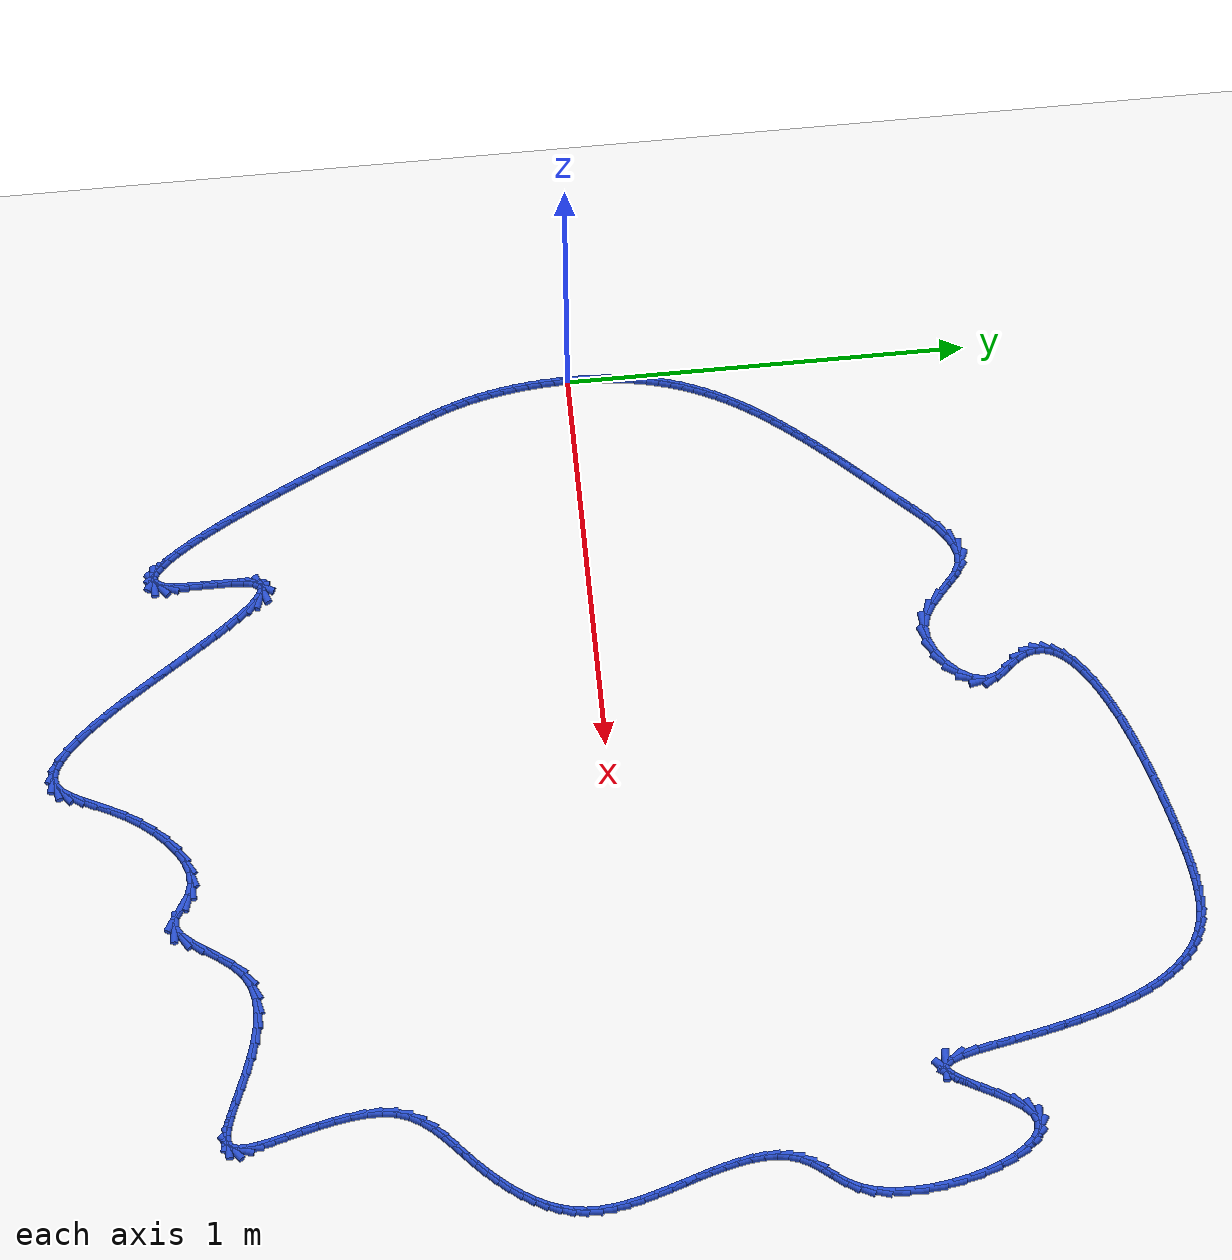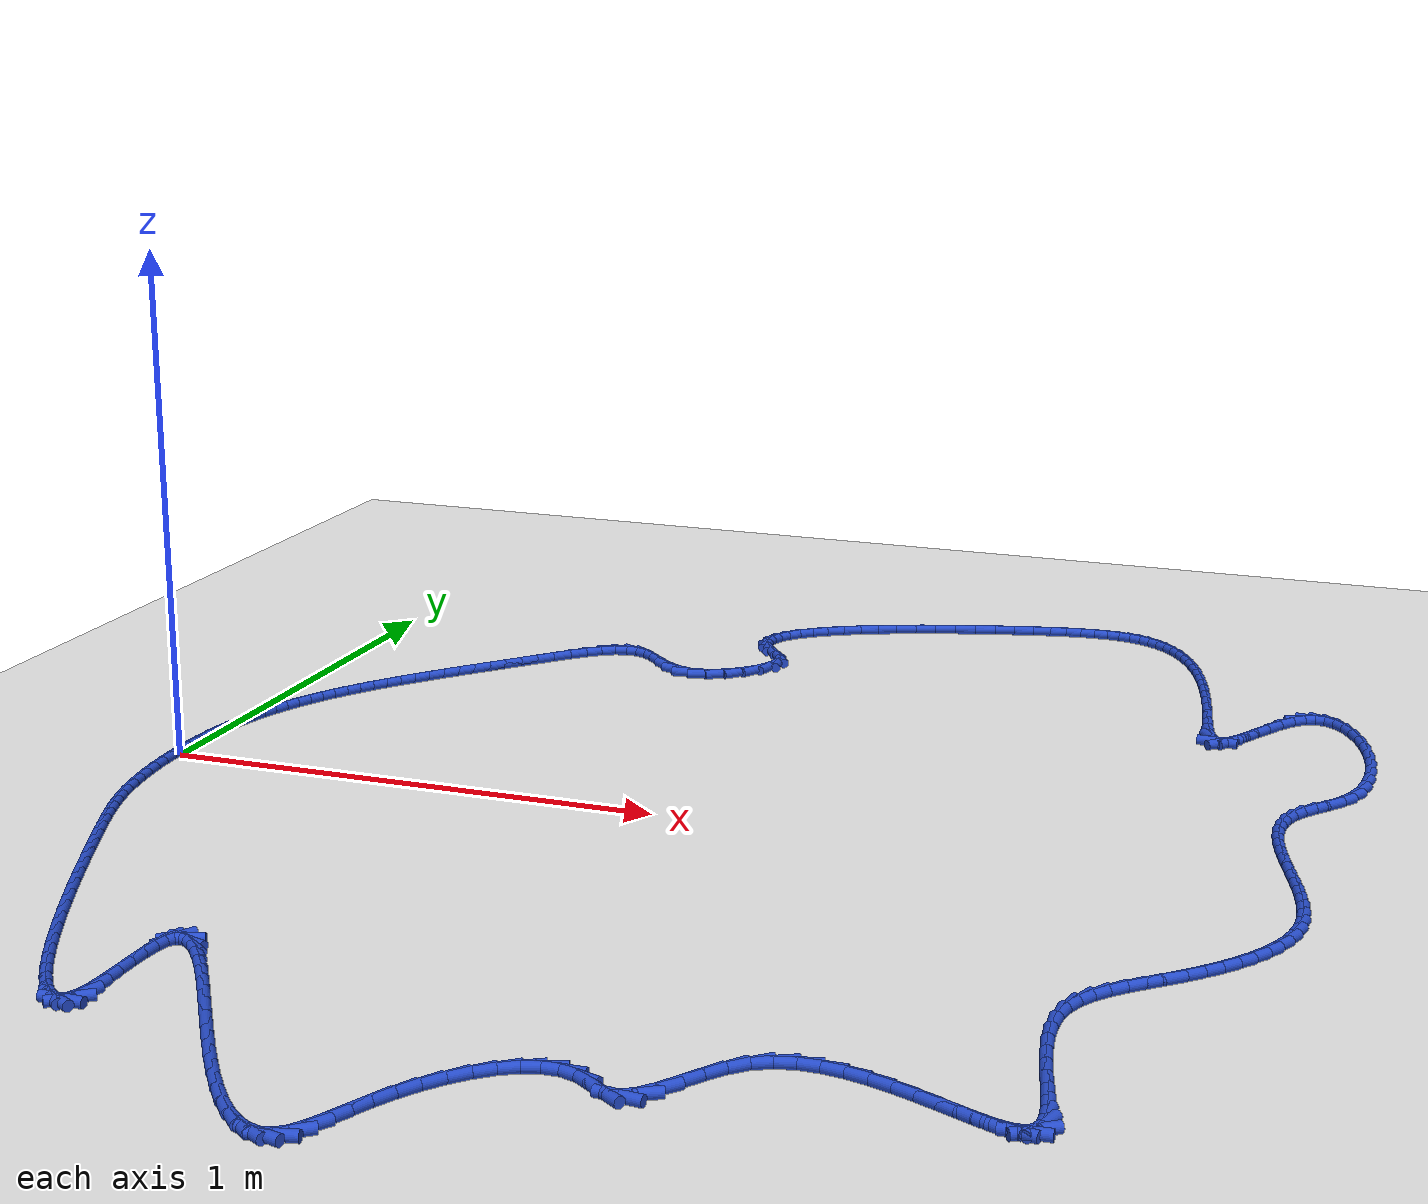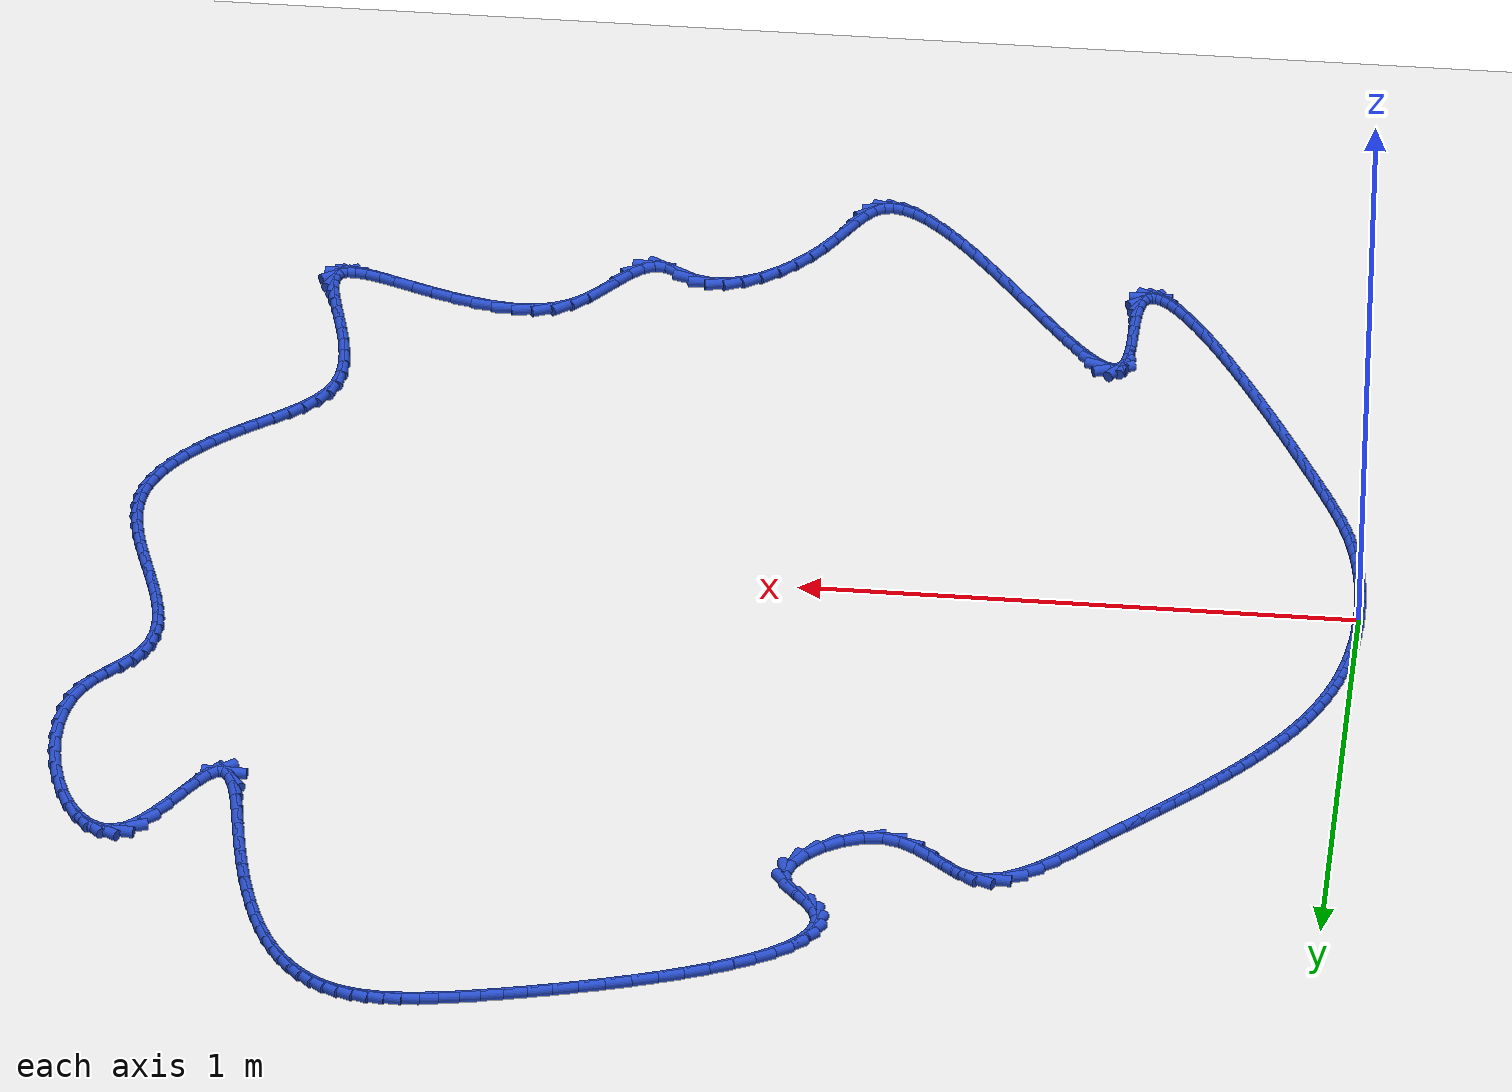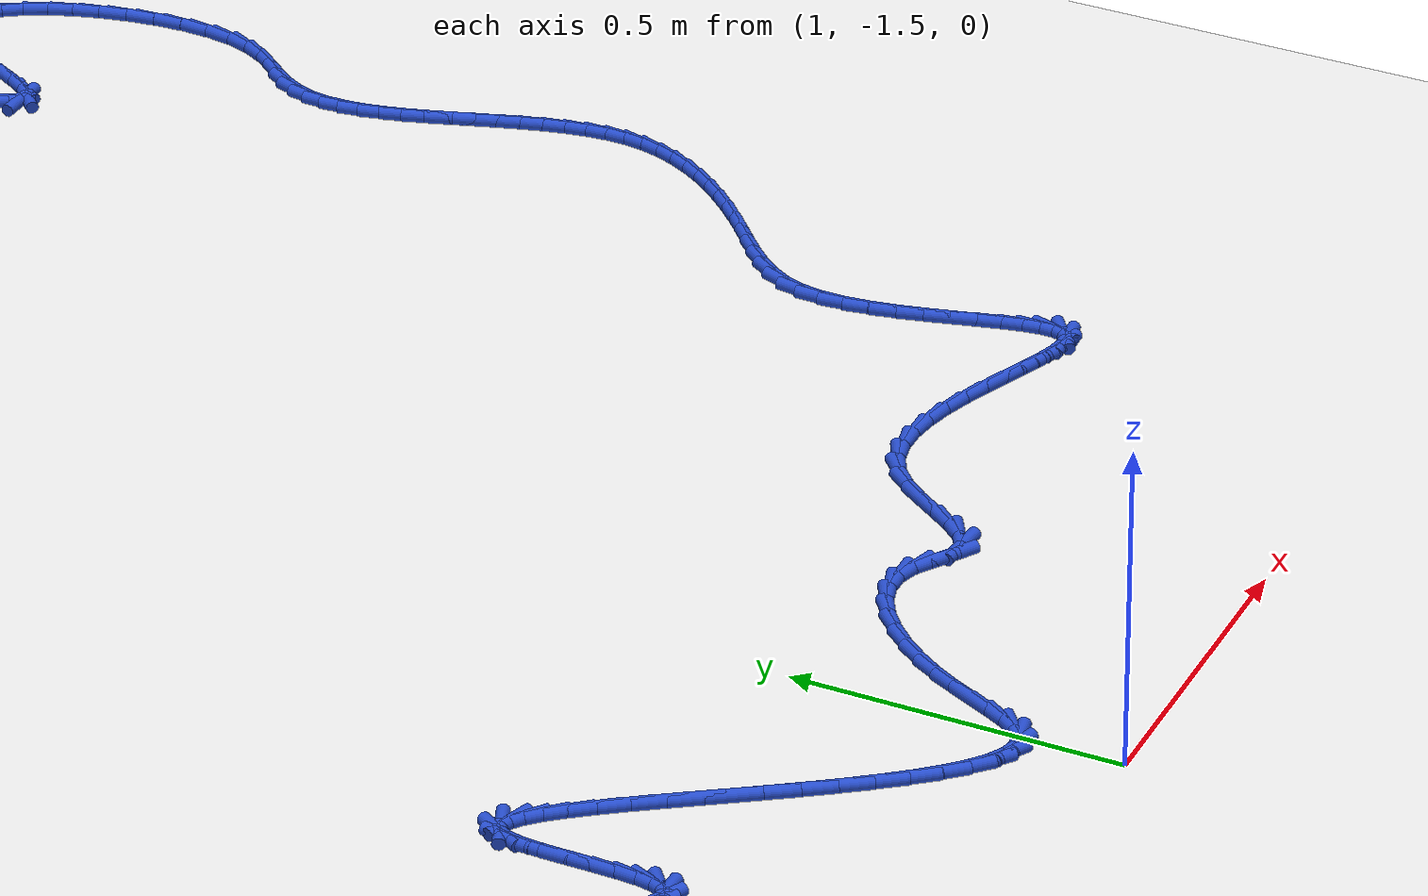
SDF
<sdf version="1.6">
 <world name="default">
  <light name="sun" type="directional">
   <pose>0 0 10 0 -0 0</pose>
   <diffuse>0.8 0.8 0.8 1</diffuse>
   <specular>0.2 0.2 0.2 1</specular>
   <attenuation>
    <range>1000</range>
    <constant>0.9</constant>
    <linear>0.01</linear>
    <quadratic>0.001</quadratic>
   </attenuation>
   <direction>-0.5 0.1 -0.9</direction>
  </light>
  <model name="ground_plane">
   <static>1</static>
   <link name="link">
    <collision name="collision">
     <geometry><plane><normal>0 0 1</normal><size>100 100</size></plane></geometry>
     <surface><friction><ode><mu>100</mu><mu2>50</mu2></ode></friction></surface>
    </collision>
    <visual name="visual">
     <cast_shadows>0</cast_shadows>
     <geometry><plane><normal>0 0 1</normal><size>100 100</size></plane></geometry>
     <material>
      <script><uri>file://media/materials/scripts/gazebo.material</uri><name>Gazebo/WhiteGlow</name></script>
     </material>
    </visual>
   </link>
  </model>
  <gravity>0 0 -9.8</gravity>
  <magnetic_field>6e-06 2.3e-05 -4.2e-05</magnetic_field>
  <atmosphere type="adiabatic"/>
  <physics name="default_physics" default="0" type="ode">
   <max_step_size>0.001</max_step_size>
   <real_time_factor>1</real_time_factor>
   <real_time_update_rate>1000</real_time_update_rate>
  </physics>
  <scene><ambient>0.4 0.4 0.4 1</ambient><background>0.7 0.7 0.7 1</background><shadows>1</shadows></scene>
  <spherical_coordinates>
   <surface_model>EARTH_WGS84</surface_model>
   <latitude_deg>0</latitude_deg>
   <longitude_deg>0</longitude_deg>
   <elevation>0</elevation>
   <heading_deg>0</heading_deg>
  </spherical_coordinates>
  <model name="line">
   <link name="link_0">
    <pose>-8.239936510889834e-18 6.938893903907228e-17 0.01 0 1.57 1.5603650162208273</pose>
    <collision name="collision">
     <geometry><cylinder><radius>0.01</radius><length>0.08</length></cylinder></geometry>
    </collision>
    <visual name="visual">
     <material>
      <script><name>Gazebo/Blue</name><uri>file://media/materials/scripts/gazebo.material</uri></script>
     </material>
     <geometry><cylinder><radius>0.01</radius><length>0.08</length></cylinder></geometry>
    </visual>
   </link>
   <link name="link_1">
    <pose>0.0003492366816804725 0.03347844089519005 0.01 0 1.57 1.5278373648724606</pose>
    <collision name="collision">
     <geometry><cylinder><radius>0.01</radius><length>0.08</length></cylinder></geometry>
    </collision>
    <visual name="visual">
     <material>
      <script><name>Gazebo/Blue</name><uri>file://media/materials/scripts/gazebo.material</uri></script>
     </material>
     <geometry><cylinder><radius>0.01</radius><length>0.08</length></cylinder></geometry>
    </visual>
   </link>
   <link name="link_2">
    <pose>0.0017802257063071424 0.06676855240438835 0.01 0 1.57 1.49415947058637</pose>
    <collision name="collision">
     <geometry><cylinder><radius>0.01</radius><length>0.08</length></cylinder></geometry>
    </collision>
    <visual name="visual">
     <material>
      <script><name>Gazebo/Blue</name><uri>file://media/materials/scripts/gazebo.material</uri></script>
     </material>
     <geometry><cylinder><radius>0.01</radius><length>0.08</length></cylinder></geometry>
    </visual>
   </link>
   <link name="link_3">
    <pose>0.004313374156254398 0.09975773537036464 0.01 0 1.57 1.4590416021160324</pose>
    <collision name="collision">
     <geometry><cylinder><radius>0.01</radius><length>0.08</length></cylinder></geometry>
    </collision>
    <visual name="visual">
     <material>
      <script><name>Gazebo/Blue</name><uri>file://media/materials/scripts/gazebo.material</uri></script>
     </material>
     <geometry><cylinder><radius>0.01</radius><length>0.08</length></cylinder></geometry>
    </visual>
   </link>
   <link name="link_4">
    <pose>0.00796908911389663 0.13233339063588856 0.01 0 1.57 1.4221731137450164</pose>
    <collision name="collision">
     <geometry><cylinder><radius>0.01</radius><length>0.08</length></cylinder></geometry>
    </collision>
    <visual name="visual">
     <material>
      <script><name>Gazebo/Blue</name><uri>file://media/materials/scripts/gazebo.material</uri></script>
     </material>
     <geometry><cylinder><radius>0.01</radius><length>0.08</length></cylinder></geometry>
    </visual>
   </link>
   <link name="link_5">
    <pose>0.012767777661608241 0.16438291904372976 0.01 0 1.57 1.3832182331818017</pose>
    <collision name="collision">
     <geometry><cylinder><radius>0.01</radius><length>0.08</length></cylinder></geometry>
    </collision>
    <visual name="visual">
     <material>
      <script><name>Gazebo/Blue</name><uri>file://media/materials/scripts/gazebo.material</uri></script>
     </material>
     <geometry><cylinder><radius>0.01</radius><length>0.08</length></cylinder></geometry>
    </visual>
   </link>
   <link name="link_6">
    <pose>0.018729846881763625 0.19579372143665794 0.01 0 1.57 1.341812516813903</pose>
    <collision name="collision">
     <geometry><cylinder><radius>0.01</radius><length>0.08</length></cylinder></geometry>
    </collision>
    <visual name="visual">
     <material>
      <script><name>Gazebo/Blue</name><uri>file://media/materials/scripts/gazebo.material</uri></script>
     </material>
     <geometry><cylinder><radius>0.01</radius><length>0.08</length></cylinder></geometry>
    </visual>
   </link>
   <link name="link_7">
    <pose>0.025875703856737174 0.22645319865744276 0.01 0 1.57 1.2979054790260176</pose>
    <collision name="collision">
     <geometry><cylinder><radius>0.01</radius><length>0.08</length></cylinder></geometry>
    </collision>
    <visual name="visual">
     <material>
      <script><name>Gazebo/Blue</name><uri>file://media/materials/scripts/gazebo.material</uri></script>
     </material>
     <geometry><cylinder><radius>0.01</radius><length>0.08</length></cylinder></geometry>
    </visual>
   </link>
   <link name="link_8">
    <pose>0.03422043899816748 0.25626935760863206 0.01 0 1.57 1.2534674418860816</pose>
    <collision name="collision">
     <geometry><cylinder><radius>0.01</radius><length>0.08</length></cylinder></geometry>
    </collision>
    <visual name="visual">
     <material>
      <script><name>Gazebo/Blue</name><uri>file://media/materials/scripts/gazebo.material</uri></script>
     </material>
     <geometry><cylinder><radius>0.01</radius><length>0.08</length></cylinder></geometry>
    </visual>
   </link>
   <link name="link_9">
    <pose>0.0437468328049661 0.2852754301740006 0.01 0 1.57 1.20969935532452</pose>
    <collision name="collision">
     <geometry><cylinder><radius>0.01</radius><length>0.08</length></cylinder></geometry>
    </collision>
    <visual name="visual">
     <material>
      <script><name>Gazebo/Blue</name><uri>file://media/materials/scripts/gazebo.material</uri></script>
     </material>
     <geometry><cylinder><radius>0.01</radius><length>0.08</length></cylinder></geometry>
    </visual>
   </link>
   <link name="link_10">
    <pose>0.054425527028528556 0.31355169492675966 0.01 0 1.57 1.1670809641107553</pose>
    <collision name="collision">
     <geometry><cylinder><radius>0.01</radius><length>0.08</length></cylinder></geometry>
    </collision>
    <visual name="visual">
     <material>
      <script><name>Gazebo/Blue</name><uri>file://media/materials/scripts/gazebo.material</uri></script>
     </material>
     <geometry><cylinder><radius>0.01</radius><length>0.08</length></cylinder></geometry>
    </visual>
   </link>
   <link name="link_11">
    <pose>0.06622714166069767 0.34117851477459826 0.01 0 1.57 1.126060294514535</pose>
    <collision name="collision">
     <geometry><cylinder><radius>0.01</radius><length>0.08</length></cylinder></geometry>
    </collision>
    <visual name="visual">
     <material>
      <script><name>Gazebo/Blue</name><uri>file://media/materials/scripts/gazebo.material</uri></script>
     </material>
     <geometry><cylinder><radius>0.01</radius><length>0.08</length></cylinder></geometry>
    </visual>
   </link>
   <link name="link_12">
    <pose>0.07912229669331619 0.3682362526252048 0.01 0 1.57 1.0870371923191466</pose>
    <collision name="collision">
     <geometry><cylinder><radius>0.01</radius><length>0.08</length></cylinder></geometry>
    </collision>
    <visual name="visual">
     <material>
      <script><name>Gazebo/Blue</name><uri>file://media/materials/scripts/gazebo.material</uri></script>
     </material>
     <geometry><cylinder><radius>0.01</radius><length>0.08</length></cylinder></geometry>
    </visual>
   </link>
   <link name="link_13">
    <pose>0.09308161211822683 0.39480527138626803 0.01 0 1.57 1.050350258451943</pose>
    <collision name="collision">
     <geometry><cylinder><radius>0.01</radius><length>0.08</length></cylinder></geometry>
    </collision>
    <visual name="visual">
     <material>
      <script><name>Gazebo/Blue</name><uri>file://media/materials/scripts/gazebo.material</uri></script>
     </material>
     <geometry><cylinder><radius>0.01</radius><length>0.08</length></cylinder></geometry>
    </visual>
   </link>
   <link name="link_14">
    <pose>0.10807570792727247 0.42096593396547655 0.01 0 1.57 1.0162693456959981</pose>
    <collision name="collision">
     <geometry><cylinder><radius>0.01</radius><length>0.08</length></cylinder></geometry>
    </collision>
    <visual name="visual">
     <material>
      <script><name>Gazebo/Blue</name><uri>file://media/materials/scripts/gazebo.material</uri></script>
     </material>
     <geometry><cylinder><radius>0.01</radius><length>0.08</length></cylinder></geometry>
    </visual>
   </link>
   <link name="link_15">
    <pose>0.12407520411229576 0.44679860327051885 0.01 0 1.57 0.9849934910647616</pose>
    <collision name="collision">
     <geometry><cylinder><radius>0.01</radius><length>0.08</length></cylinder></geometry>
    </collision>
    <visual name="visual">
     <material>
      <script><name>Gazebo/Blue</name><uri>file://media/materials/scripts/gazebo.material</uri></script>
     </material>
     <geometry><cylinder><radius>0.01</radius><length>0.08</length></cylinder></geometry>
    </visual>
   </link>
   <link name="link_16">
    <pose>0.14105072066513952 0.47238364220908363 0.01 0 1.57 0.9566534719963925</pose>
    <collision name="collision">
     <geometry><cylinder><radius>0.01</radius><length>0.08</length></cylinder></geometry>
    </collision>
    <visual name="visual">
     <material>
      <script><name>Gazebo/Blue</name><uri>file://media/materials/scripts/gazebo.material</uri></script>
     </material>
     <geometry><cylinder><radius>0.01</radius><length>0.08</length></cylinder></geometry>
    </visual>
   </link>
   <link name="link_17">
    <pose>0.15897287757764655 0.49780141368885944 0.01 0 1.57 0.9313177812842572</pose>
    <collision name="collision">
     <geometry><cylinder><radius>0.01</radius><length>0.08</length></cylinder></geometry>
    </collision>
    <visual name="visual">
     <material>
      <script><name>Gazebo/Blue</name><uri>file://media/materials/scripts/gazebo.material</uri></script>
     </material>
     <geometry><cylinder><radius>0.01</radius><length>0.08</length></cylinder></geometry>
    </visual>
   </link>
   <link name="link_18">
    <pose>0.17781229484165956 0.5231322806175349 0.01 0 1.57 0.909000715635817</pose>
    <collision name="collision">
     <geometry><cylinder><radius>0.01</radius><length>0.08</length></cylinder></geometry>
    </collision>
    <visual name="visual">
     <material>
      <script><name>Gazebo/Blue</name><uri>file://media/materials/scripts/gazebo.material</uri></script>
     </material>
     <geometry><cylinder><radius>0.01</radius><length>0.08</length></cylinder></geometry>
    </visual>
   </link>
   <link name="link_19">
    <pose>0.19753959244902136 0.5484566059027987 0.01 0 1.57 0.8896713961067251</pose>
    <collision name="collision">
     <geometry><cylinder><radius>0.01</radius><length>0.08</length></cylinder></geometry>
    </collision>
    <visual name="visual">
     <material>
      <script><name>Gazebo/Blue</name><uri>file://media/materials/scripts/gazebo.material</uri></script>
     </material>
     <geometry><cylinder><radius>0.01</radius><length>0.08</length></cylinder></geometry>
    </visual>
   </link>
   <link name="link_20">
    <pose>0.21812539039157466 0.5738547524523392 0.01 0 1.57 0.8732627892761352</pose>
    <collision name="collision">
     <geometry><cylinder><radius>0.01</radius><length>0.08</length></cylinder></geometry>
    </collision>
    <visual name="visual">
     <material>
      <script><name>Gazebo/Blue</name><uri>file://media/materials/scripts/gazebo.material</uri></script>
     </material>
     <geometry><cylinder><radius>0.01</radius><length>0.08</length></cylinder></geometry>
    </visual>
   </link>
   <link name="link_21">
    <pose>0.23954030866116238 0.5994070831738456 0.01 0 1.57 0.8596800883892945</pose>
    <collision name="collision">
     <geometry><cylinder><radius>0.01</radius><length>0.08</length></cylinder></geometry>
    </collision>
    <visual name="visual">
     <material>
      <script><name>Gazebo/Blue</name><uri>file://media/materials/scripts/gazebo.material</uri></script>
     </material>
     <geometry><cylinder><radius>0.01</radius><length>0.08</length></cylinder></geometry>
    </visual>
   </link>
   <link name="link_22">
    <pose>0.26175496724962716 0.6251939609750059 0.01 0 1.57 0.8488080826642873</pose>
    <collision name="collision">
     <geometry><cylinder><radius>0.01</radius><length>0.08</length></cylinder></geometry>
    </collision>
    <visual name="visual">
     <material>
      <script><name>Gazebo/Blue</name><uri>file://media/materials/scripts/gazebo.material</uri></script>
     </material>
     <geometry><cylinder><radius>0.01</radius><length>0.08</length></cylinder></geometry>
    </visual>
   </link>
   <link name="link_23">
    <pose>0.2847399861488117 0.6512957487635088 0.01 0 1.57 0.8405173584820748</pose>
    <collision name="collision">
     <geometry><cylinder><radius>0.01</radius><length>0.08</length></cylinder></geometry>
    </collision>
    <visual name="visual">
     <material>
      <script><name>Gazebo/Blue</name><uri>file://media/materials/scripts/gazebo.material</uri></script>
     </material>
     <geometry><cylinder><radius>0.01</radius><length>0.08</length></cylinder></geometry>
    </visual>
   </link>
   <link name="link_24">
    <pose>0.3084659853505589 0.6777928094470432 0.01 0 1.57 0.8346693291970123</pose>
    <collision name="collision">
     <geometry><cylinder><radius>0.01</radius><length>0.08</length></cylinder></geometry>
    </collision>
    <visual name="visual">
     <material>
      <script><name>Gazebo/Blue</name><uri>file://media/materials/scripts/gazebo.material</uri></script>
     </material>
     <geometry><cylinder><radius>0.01</radius><length>0.08</length></cylinder></geometry>
    </visual>
   </link>
   <link name="link_25">
    <pose>0.3329035848467115 0.7047655059332976 0.01 0 1.57 0.8311201860196784</pose>
    <collision name="collision">
     <geometry><cylinder><radius>0.01</radius><length>0.08</length></cylinder></geometry>
    </collision>
    <visual name="visual">
     <material>
      <script><name>Gazebo/Blue</name><uri>file://media/materials/scripts/gazebo.material</uri></script>
     </material>
     <geometry><cylinder><radius>0.01</radius><length>0.08</length></cylinder></geometry>
    </visual>
   </link>
   <link name="link_26">
    <pose>0.3580234046291122 0.7322942011299605 0.01 0 1.57 0.8297239126026239</pose>
    <collision name="collision">
     <geometry><cylinder><radius>0.01</radius><length>0.08</length></cylinder></geometry>
    </collision>
    <visual name="visual">
     <material>
      <script><name>Gazebo/Blue</name><uri>file://media/materials/scripts/gazebo.material</uri></script>
     </material>
     <geometry><cylinder><radius>0.01</radius><length>0.08</length></cylinder></geometry>
    </visual>
   </link>
   <link name="link_27">
    <pose>0.383796064689604 0.7604592579447207 0.01 0 1.57 0.8303345236938219</pose>
    <collision name="collision">
     <geometry><cylinder><radius>0.01</radius><length>0.08</length></cylinder></geometry>
    </collision>
    <visual name="visual">
     <material>
      <script><name>Gazebo/Blue</name><uri>file://media/materials/scripts/gazebo.material</uri></script>
     </material>
     <geometry><cylinder><radius>0.01</radius><length>0.08</length></cylinder></geometry>
    </visual>
   </link>
   <link name="link_28">
    <pose>0.4101921850200293 0.7893410392852664 0.01 0 1.57 0.8300389786921769</pose>
    <collision name="collision">
     <geometry><cylinder><radius>0.01</radius><length>0.08</length></cylinder></geometry>
    </collision>
    <visual name="visual">
     <material>
      <script><name>Gazebo/Blue</name><uri>file://media/materials/scripts/gazebo.material</uri></script>
     </material>
     <geometry><cylinder><radius>0.01</radius><length>0.08</length></cylinder></geometry>
    </visual>
   </link>
   <link name="link_29">
    <pose>0.4371644041598142 0.8188356599635639 0.01 0 1.57 0.8106676798126445</pose>
    <collision name="collision">
     <geometry><cylinder><radius>0.01</radius><length>0.08</length></cylinder></geometry>
    </collision>
    <visual name="visual">
     <material>
      <script><name>Gazebo/Blue</name><uri>file://media/materials/scripts/gazebo.material</uri></script>
     </material>
     <geometry><cylinder><radius>0.01</radius><length>0.08</length></cylinder></geometry>
    </visual>
   </link>
   <link name="link_30">
    <pose>0.4645482928926192 0.8476396925871876 0.01 0 1.57 0.7621356927677012</pose>
    <collision name="collision">
     <geometry><cylinder><radius>0.01</radius><length>0.08</length></cylinder></geometry>
    </collision>
    <visual name="visual">
     <material>
      <script><name>Gazebo/Blue</name><uri>file://media/materials/scripts/gazebo.material</uri></script>
     </material>
     <geometry><cylinder><radius>0.01</radius><length>0.08</length></cylinder></geometry>
    </visual>
   </link>
   <link name="link_31">
    <pose>0.49213256239178854 0.8739695597865667 0.01 0 1.57 0.6750120277448454</pose>
    <collision name="collision">
     <geometry><cylinder><radius>0.01</radius><length>0.08</length></cylinder></geometry>
    </collision>
    <visual name="visual">
     <material>
      <script><name>Gazebo/Blue</name><uri>file://media/materials/scripts/gazebo.material</uri></script>
     </material>
     <geometry><cylinder><radius>0.01</radius><length>0.08</length></cylinder></geometry>
    </visual>
   </link>
   <link name="link_32">
    <pose>0.5197057995443821 0.896040410684806 0.01 0 1.57 0.5300459853184879</pose>
    <collision name="collision">
     <geometry><cylinder><radius>0.01</radius><length>0.08</length></cylinder></geometry>
    </collision>
    <visual name="visual">
     <material>
      <script><name>Gazebo/Blue</name><uri>file://media/materials/scripts/gazebo.material</uri></script>
     </material>
     <geometry><cylinder><radius>0.01</radius><length>0.08</length></cylinder></geometry>
    </visual>
   </link>
   <link name="link_33">
    <pose>0.5470565912374592 0.9120673944050098 0.01 0 1.57 0.29565012495039306</pose>
    <collision name="collision">
     <geometry><cylinder><radius>0.01</radius><length>0.08</length></cylinder></geometry>
    </collision>
    <visual name="visual">
     <material>
      <script><name>Gazebo/Blue</name><uri>file://media/materials/scripts/gazebo.material</uri></script>
     </material>
     <geometry><cylinder><radius>0.01</radius><length>0.08</length></cylinder></geometry>
    </visual>
   </link>
   <link name="link_34">
    <pose>0.573973524358079 0.9202656600702825 0.01 0 1.57 -0.05381983532159908</pose>
    <collision name="collision">
     <geometry><cylinder><radius>0.01</radius><length>0.08</length></cylinder></geometry>
    </collision>
    <visual name="visual">
     <material>
      <script><name>Gazebo/Blue</name><uri>file://media/materials/scripts/gazebo.material</uri></script>
     </material>
     <geometry><cylinder><radius>0.01</radius><length>0.08</length></cylinder></geometry>
    </visual>
   </link>
   <link name="link_35">
    <pose>0.6002451857933011 0.9188503568037286 0.01 0 1.57 -0.44125276178049466</pose>
    <collision name="collision">
     <geometry><cylinder><radius>0.01</radius><length>0.08</length></cylinder></geometry>
    </collision>
    <visual name="visual">
     <material>
      <script><name>Gazebo/Blue</name><uri>file://media/materials/scripts/gazebo.material</uri></script>
     </material>
     <geometry><cylinder><radius>0.01</radius><length>0.08</length></cylinder></geometry>
    </visual>
   </link>
   <link name="link_36">
    <pose>0.6257768149628437 0.9067914658486821 0.01 0 1.57 -0.6641257364054871</pose>
    <collision name="collision">
     <geometry><cylinder><radius>0.01</radius><length>0.08</length></cylinder></geometry>
    </collision>
    <visual name="visual">
     <material>
      <script><name>Gazebo/Blue</name><uri>file://media/materials/scripts/gazebo.material</uri></script>
     </material>
     <geometry><cylinder><radius>0.01</radius><length>0.08</length></cylinder></geometry>
    </visual>
   </link>
   <link name="link_37">
    <pose>0.6510804429153761 0.8869853796577263 0.01 0 1.57 -0.7366234121169817</pose>
    <collision name="collision">
     <geometry><cylinder><radius>0.01</radius><length>0.08</length></cylinder></geometry>
    </collision>
    <visual name="visual">
     <material>
      <script><name>Gazebo/Blue</name><uri>file://media/materials/scripts/gazebo.material</uri></script>
     </material>
     <geometry><cylinder><radius>0.01</radius><length>0.08</length></cylinder></geometry>
    </visual>
   </link>
   <link name="link_38">
    <pose>0.6768647764408978 0.8636011348639187 0.01 0 1.57 -0.7015799820788591</pose>
    <collision name="collision">
     <geometry><cylinder><radius>0.01</radius><length>0.08</length></cylinder></geometry>
    </collision>
    <visual name="visual">
     <material>
      <script><name>Gazebo/Blue</name><uri>file://media/materials/scripts/gazebo.material</uri></script>
     </material>
     <geometry><cylinder><radius>0.01</radius><length>0.08</length></cylinder></geometry>
    </visual>
   </link>
   <link name="link_39">
    <pose>0.7038386239582457 0.8408084257175098 0.01 0 1.57 -0.5582598452492732</pose>
    <collision name="collision">
     <geometry><cylinder><radius>0.01</radius><length>0.08</length></cylinder></geometry>
    </collision>
    <visual name="visual">
     <material>
      <script><name>Gazebo/Blue</name><uri>file://media/materials/scripts/gazebo.material</uri></script>
     </material>
     <geometry><cylinder><radius>0.01</radius><length>0.08</length></cylinder></geometry>
    </visual>
   </link>
   <link name="link_40">
    <pose>0.7327107938862562 0.82277694646875 0.01 0 1.57 -0.2814237937702085</pose>
    <collision name="collision">
     <geometry><cylinder><radius>0.01</radius><length>0.08</length></cylinder></geometry>
    </collision>
    <visual name="visual">
     <material>
      <script><name>Gazebo/Blue</name><uri>file://media/materials/scripts/gazebo.material</uri></script>
     </material>
     <geometry><cylinder><radius>0.01</radius><length>0.08</length></cylinder></geometry>
    </visual>
   </link>
   <link name="link_41">
    <pose>0.7641900946437672 0.8136763913678896 0.01 0 1.57 0.08965125298206376</pose>
    <collision name="collision">
     <geometry><cylinder><radius>0.01</radius><length>0.08</length></cylinder></geometry>
    </collision>
    <visual name="visual">
     <material>
      <script><name>Gazebo/Blue</name><uri>file://media/materials/scripts/gazebo.material</uri></script>
     </material>
     <geometry><cylinder><radius>0.01</radius><length>0.08</length></cylinder></geometry>
    </visual>
   </link>
   <link name="link_42">
    <pose>0.7984862409195749 0.8167593478803035 0.01 0 1.57 0.38286554177662313</pose>
    <collision name="collision">
     <geometry><cylinder><radius>0.01</radius><length>0.08</length></cylinder></geometry>
    </collision>
    <visual name="visual">
     <material>
      <script><name>Gazebo/Blue</name><uri>file://media/materials/scripts/gazebo.material</uri></script>
     </material>
     <geometry><cylinder><radius>0.01</radius><length>0.08</length></cylinder></geometry>
    </visual>
   </link>
   <link name="link_43">
    <pose>0.8333781376916977 0.8308116832055819 0.01 0 1.57 0.6041011716048205</pose>
    <collision name="collision">
     <geometry><cylinder><radius>0.01</radius><length>0.08</length></cylinder></geometry>
    </collision>
    <visual name="visual">
     <material>
      <script><name>Gazebo/Blue</name><uri>file://media/materials/scripts/gazebo.material</uri></script>
     </material>
     <geometry><cylinder><radius>0.01</radius><length>0.08</length></cylinder></geometry>
    </visual>
   </link>
   <link name="link_44">
    <pose>0.8659057337419693 0.8532613998769096 0.01 0 1.57 0.8047136071499122</pose>
    <collision name="collision">
     <geometry><cylinder><radius>0.01</radius><length>0.08</length></cylinder></geometry>
    </collision>
    <visual name="visual">
     <material>
      <script><name>Gazebo/Blue</name><uri>file://media/materials/scripts/gazebo.material</uri></script>
     </material>
     <geometry><cylinder><radius>0.01</radius><length>0.08</length></cylinder></geometry>
    </visual>
   </link>
   <link name="link_45">
    <pose>0.8931088062607991 0.8815361851206437 0.01 0 1.57 1.0303348112776927</pose>
    <collision name="collision">
     <geometry><cylinder><radius>0.01</radius><length>0.08</length></cylinder></geometry>
    </collision>
    <visual name="visual">
     <material>
      <script><name>Gazebo/Blue</name><uri>file://media/materials/scripts/gazebo.material</uri></script>
     </material>
     <geometry><cylinder><radius>0.01</radius><length>0.08</length></cylinder></geometry>
    </visual>
   </link>
   <link name="link_46">
    <pose>0.912027132438595 0.9130637261631414 0.01 0 1.57 1.336912426205885</pose>
    <collision name="collision">
     <geometry><cylinder><radius>0.01</radius><length>0.08</length></cylinder></geometry>
    </collision>
    <visual name="visual">
     <material>
      <script><name>Gazebo/Blue</name><uri>file://media/materials/scripts/gazebo.material</uri></script>
     </material>
     <geometry><cylinder><radius>0.01</radius><length>0.08</length></cylinder></geometry>
    </visual>
   </link>
   <link name="link_47">
    <pose>0.919700489465766 0.9452717102307596 0.01 0 1.57 -1.3618487671296438</pose>
    <collision name="collision">
     <geometry><cylinder><radius>0.01</radius><length>0.08</length></cylinder></geometry>
    </collision>
    <visual name="visual">
     <material>
      <script><name>Gazebo/Blue</name><uri>file://media/materials/scripts/gazebo.material</uri></script>
     </material>
     <geometry><cylinder><radius>0.01</radius><length>0.08</length></cylinder></geometry>
    </visual>
   </link>
   <link name="link_48">
    <pose>0.9132661326690819 0.9756163754162838 0.01 0 1.57 -0.9794050983664577</pose>
    <collision name="collision">
     <geometry><cylinder><radius>0.01</radius><length>0.08</length></cylinder></geometry>
    </collision>
    <visual name="visual">
     <material>
      <script><name>Gazebo/Blue</name><uri>file://media/materials/scripts/gazebo.material</uri></script>
     </material>
     <geometry><cylinder><radius>0.01</radius><length>0.08</length></cylinder></geometry>
    </visual>
   </link>
   <link name="link_49">
    <pose>0.8948632785258921 1.0030190096177318 0.01 0 1.57 -0.8838972463474902</pose>
    <collision name="collision">
     <geometry><cylinder><radius>0.01</radius><length>0.08</length></cylinder></geometry>
    </collision>
    <visual name="visual">
     <material>
      <script><name>Gazebo/Blue</name><uri>file://media/materials/scripts/gazebo.material</uri></script>
     </material>
     <geometry><cylinder><radius>0.01</radius><length>0.08</length></cylinder></geometry>
    </visual>
   </link>
   <link name="link_50">
    <pose>0.8739329485953989 1.0285395635077748 0.01 0 1.57 -1.0335879980780518</pose>
    <collision name="collision">
     <geometry><cylinder><radius>0.01</radius><length>0.08</length></cylinder></geometry>
    </collision>
    <visual name="visual">
     <material>
      <script><name>Gazebo/Blue</name><uri>file://media/materials/scripts/gazebo.material</uri></script>
     </material>
     <geometry><cylinder><radius>0.01</radius><length>0.08</length></cylinder></geometry>
    </visual>
   </link>
   <link name="link_51">
    <pose>0.8592115667278005 1.053254747948973 0.01 0 1.57 -1.29859569289673</pose>
    <collision name="collision">
     <geometry><cylinder><radius>0.01</radius><length>0.08</length></cylinder></geometry>
    </collision>
    <visual name="visual">
     <material>
      <script><name>Gazebo/Blue</name><uri>file://media/materials/scripts/gazebo.material</uri></script>
     </material>
     <geometry><cylinder><radius>0.01</radius><length>0.08</length></cylinder></geometry>
    </visual>
   </link>
   <link name="link_52">
    <pose>0.8524684329561548 1.0774125359403435 0.01 0 1.57 1.5432106980710691</pose>
    <collision name="collision">
     <geometry><cylinder><radius>0.01</radius><length>0.08</length></cylinder></geometry>
    </collision>
    <visual name="visual">
     <material>
      <script><name>Gazebo/Blue</name><uri>file://media/materials/scripts/gazebo.material</uri></script>
     </material>
     <geometry><cylinder><radius>0.01</radius><length>0.08</length></cylinder></geometry>
    </visual>
   </link>
   <link name="link_53">
    <pose>0.8531187455249725 1.100980880584885 0.01 0 1.57 1.2565857160745957</pose>
    <collision name="collision">
     <geometry><cylinder><radius>0.01</radius><length>0.08</length></cylinder></geometry>
    </collision>
    <visual name="visual">
     <material>
      <script><name>Gazebo/Blue</name><uri>file://media/materials/scripts/gazebo.material</uri></script>
     </material>
     <geometry><cylinder><radius>0.01</radius><length>0.08</length></cylinder></geometry>
    </visual>
   </link>
   <link name="link_54">
    <pose>0.8605758619552474 1.1239275160319369 0.01 0 1.57 1.0204856344525668</pose>
    <collision name="collision">
     <geometry><cylinder><radius>0.01</radius><length>0.08</length></cylinder></geometry>
    </collision>
    <visual name="visual">
     <material>
      <script><name>Gazebo/Blue</name><uri>file://media/materials/scripts/gazebo.material</uri></script>
     </material>
     <geometry><cylinder><radius>0.01</radius><length>0.08</length></cylinder></geometry>
    </visual>
   </link>
   <link name="link_55">
    <pose>0.8742531397679729 1.1462201764308364 0.01 0 1.57 0.8414434889442308</pose>
    <collision name="collision">
     <geometry><cylinder><radius>0.01</radius><length>0.08</length></cylinder></geometry>
    </collision>
    <visual name="visual">
     <material>
      <script><name>Gazebo/Blue</name><uri>file://media/materials/scripts/gazebo.material</uri></script>
     </material>
     <geometry><cylinder><radius>0.01</radius><length>0.08</length></cylinder></geometry>
    </visual>
   </link>
   <link name="link_56">
    <pose>0.893563936484142 1.1678265959309213 0.01 0 1.57 0.7088606977462394</pose>
    <collision name="collision">
     <geometry><cylinder><radius>0.01</radius><length>0.08</length></cylinder></geometry>
    </collision>
    <visual name="visual">
     <material>
      <script><name>Gazebo/Blue</name><uri>file://media/materials/scripts/gazebo.material</uri></script>
     </material>
     <geometry><cylinder><radius>0.01</radius><length>0.08</length></cylinder></geometry>
    </visual>
   </link>
   <link name="link_57">
    <pose>0.917921609624748 1.1887145086815298 0.01 0 1.57 0.6099011780740867</pose>
    <collision name="collision">
     <geometry><cylinder><radius>0.01</radius><length>0.08</length></cylinder></geometry>
    </collision>
    <visual name="visual">
     <material>
      <script><name>Gazebo/Blue</name><uri>file://media/materials/scripts/gazebo.material</uri></script>
     </material>
     <geometry><cylinder><radius>0.01</radius><length>0.08</length></cylinder></geometry>
    </visual>
   </link>
   <link name="link_58">
    <pose>0.9467395167107846 1.2088516488319991 0.01 0 1.57 0.5345330191964237</pose>
    <collision name="collision">
     <geometry><cylinder><radius>0.01</radius><length>0.08</length></cylinder></geometry>
    </collision>
    <visual name="visual">
     <material>
      <script><name>Gazebo/Blue</name><uri>file://media/materials/scripts/gazebo.material</uri></script>
     </material>
     <geometry><cylinder><radius>0.01</radius><length>0.08</length></cylinder></geometry>
    </visual>
   </link>
   <link name="link_59">
    <pose>0.9794310152632452 1.2282057505316684 0.01 0 1.57 0.47579286345281796</pose>
    <collision name="collision">
     <geometry><cylinder><radius>0.01</radius><length>0.08</length></cylinder></geometry>
    </collision>
    <visual name="visual">
     <material>
      <script><name>Gazebo/Blue</name><uri>file://media/materials/scripts/gazebo.material</uri></script>
     </material>
     <geometry><cylinder><radius>0.01</radius><length>0.08</length></cylinder></geometry>
    </visual>
   </link>
   <link name="link_60">
    <pose>1.0154094628031232 1.2467445479298744 0.01 0 1.57 0.4289814032866932</pose>
    <collision name="collision">
     <geometry><cylinder><radius>0.01</radius><length>0.08</length></cylinder></geometry>
    </collision>
    <visual name="visual">
     <material>
      <script><name>Gazebo/Blue</name><uri>file://media/materials/scripts/gazebo.material</uri></script>
     </material>
     <geometry><cylinder><radius>0.01</radius><length>0.08</length></cylinder></geometry>
    </visual>
   </link>
   <link name="link_61">
    <pose>1.0540882168514116 1.264435775175956 0.01 0 1.57 0.390911209791771</pose>
    <collision name="collision">
     <geometry><cylinder><radius>0.01</radius><length>0.08</length></cylinder></geometry>
    </collision>
    <visual name="visual">
     <material>
      <script><name>Gazebo/Blue</name><uri>file://media/materials/scripts/gazebo.material</uri></script>
     </material>
     <geometry><cylinder><radius>0.01</radius><length>0.08</length></cylinder></geometry>
    </visual>
   </link>
   <link name="link_62">
    <pose>1.094880634929104 1.2812471664192504 0.01 0 1.57 0.35938165832704916</pose>
    <collision name="collision">
     <geometry><cylinder><radius>0.01</radius><length>0.08</length></cylinder></geometry>
    </collision>
    <visual name="visual">
     <material>
      <script><name>Gazebo/Blue</name><uri>file://media/materials/scripts/gazebo.material</uri></script>
     </material>
     <geometry><cylinder><radius>0.01</radius><length>0.08</length></cylinder></geometry>
    </visual>
   </link>
   <link name="link_63">
    <pose>1.1372000745571942 1.297146455809096 0.01 0 1.57 0.33283900901021535</pose>
    <collision name="collision">
     <geometry><cylinder><radius>0.01</radius><length>0.08</length></cylinder></geometry>
    </collision>
    <visual name="visual">
     <material>
      <script><name>Gazebo/Blue</name><uri>file://media/materials/scripts/gazebo.material</uri></script>
     </material>
     <geometry><cylinder><radius>0.01</radius><length>0.08</length></cylinder></geometry>
    </visual>
   </link>
   <link name="link_64">
    <pose>1.1804598932566748 1.3121013774948298 0.01 0 1.57 0.3101594216612146</pose>
    <collision name="collision">
     <geometry><cylinder><radius>0.01</radius><length>0.08</length></cylinder></geometry>
    </collision>
    <visual name="visual">
     <material>
      <script><name>Gazebo/Blue</name><uri>file://media/materials/scripts/gazebo.material</uri></script>
     </material>
     <geometry><cylinder><radius>0.01</radius><length>0.08</length></cylinder></geometry>
    </visual>
   </link>
   <link name="link_65">
    <pose>1.2240734485485394 1.3260796656257907 0.01 0 1.57 0.2905089482103704</pose>
    <collision name="collision">
     <geometry><cylinder><radius>0.01</radius><length>0.08</length></cylinder></geometry>
    </collision>
    <visual name="visual">
     <material>
      <script><name>Gazebo/Blue</name><uri>file://media/materials/scripts/gazebo.material</uri></script>
     </material>
     <geometry><cylinder><radius>0.01</radius><length>0.08</length></cylinder></geometry>
    </visual>
   </link>
   <link name="link_66">
    <pose>1.267454097953782 1.3390490543513165 0.01 0 1.57 0.2732508585352861</pose>
    <collision name="collision">
     <geometry><cylinder><radius>0.01</radius><length>0.08</length></cylinder></geometry>
    </collision>
    <visual name="visual">
     <material>
      <script><name>Gazebo/Blue</name><uri>file://media/materials/scripts/gazebo.material</uri></script>
     </material>
     <geometry><cylinder><radius>0.01</radius><length>0.08</length></cylinder></geometry>
    </visual>
   </link>
   <link name="link_67">
    <pose>1.3100151989933952 1.350977277820745 0.01 0 1.57 0.2578815889737345</pose>
    <collision name="collision">
     <geometry><cylinder><radius>0.01</radius><length>0.08</length></cylinder></geometry>
    </collision>
    <visual name="visual">
     <material>
      <script><name>Gazebo/Blue</name><uri>file://media/materials/scripts/gazebo.material</uri></script>
     </material>
     <geometry><cylinder><radius>0.01</radius><length>0.08</length></cylinder></geometry>
    </visual>
   </link>
   <link name="link_68">
    <pose>1.351170109188373 1.3618320701834135 0.01 0 1.57 0.24249999319359616</pose>
    <collision name="collision">
     <geometry><cylinder><radius>0.01</radius><length>0.08</length></cylinder></geometry>
    </collision>
    <visual name="visual">
     <material>
      <script><name>Gazebo/Blue</name><uri>file://media/materials/scripts/gazebo.material</uri></script>
     </material>
     <geometry><cylinder><radius>0.01</radius><length>0.08</length></cylinder></geometry>
    </visual>
   </link>
   <link name="link_69">
    <pose>1.3904356467151624 1.3715451091917472 0.01 0 1.57 0.22034354270858633</pose>
    <collision name="collision">
     <geometry><cylinder><radius>0.01</radius><length>0.08</length></cylinder></geometry>
    </collision>
    <visual name="visual">
     <material>
      <script><name>Gazebo/Blue</name><uri>file://media/materials/scripts/gazebo.material</uri></script>
     </material>
     <geometry><cylinder><radius>0.01</radius><length>0.08</length></cylinder></geometry>
    </visual>
   </link>
   <link name="link_70">
    <pose>1.4277472736054202 1.379902173764043 0.01 0 1.57 0.18842034385660517</pose>
    <collision name="collision">
     <geometry><cylinder><radius>0.01</radius><length>0.08</length></cylinder></geometry>
    </collision>
    <visual name="visual">
     <material>
      <script><name>Gazebo/Blue</name><uri>file://media/materials/scripts/gazebo.material</uri></script>
     </material>
     <geometry><cylinder><radius>0.01</radius><length>0.08</length></cylinder></geometry>
    </visual>
   </link>
   <link name="link_71">
    <pose>1.4631463270556389 1.3866521449567997 0.01 0 1.57 0.14487924602289468</pose>
    <collision name="collision">
     <geometry><cylinder><radius>0.01</radius><length>0.08</length></cylinder></geometry>
    </collision>
    <visual name="visual">
     <material>
      <script><name>Gazebo/Blue</name><uri>file://media/materials/scripts/gazebo.material</uri></script>
     </material>
     <geometry><cylinder><radius>0.01</radius><length>0.08</length></cylinder></geometry>
    </visual>
   </link>
   <link name="link_72">
    <pose>1.4966741442682563 1.391543903824444 0.01 0 1.57 0.08755508844286412</pose>
    <collision name="collision">
     <geometry><cylinder><radius>0.01</radius><length>0.08</length></cylinder></geometry>
    </collision>
    <visual name="visual">
     <material>
      <script><name>Gazebo/Blue</name><uri>file://media/materials/scripts/gazebo.material</uri></script>
     </material>
     <geometry><cylinder><radius>0.01</radius><length>0.08</length></cylinder></geometry>
    </visual>
   </link>
   <link name="link_73">
    <pose>1.5283720624457124 1.3943263314214003 0.01 0 1.57 0.014107605019824266</pose>
    <collision name="collision">
     <geometry><cylinder><radius>0.01</radius><length>0.08</length></cylinder></geometry>
    </collision>
    <visual name="visual">
     <material>
      <script><name>Gazebo/Blue</name><uri>file://media/materials/scripts/gazebo.material</uri></script>
     </material>
     <geometry><cylinder><radius>0.01</radius><length>0.08</length></cylinder></geometry>
    </visual>
   </link>
   <link name="link_74">
    <pose>1.5582814187904472 1.3947483088020955 0.01 0 1.57 -0.07759340521780513</pose>
    <collision name="collision">
     <geometry><cylinder><radius>0.01</radius><length>0.08</length></cylinder></geometry>
    </collision>
    <visual name="visual">
     <material>
      <script><name>Gazebo/Blue</name><uri>file://media/materials/scripts/gazebo.material</uri></script>
     </material>
     <geometry><cylinder><radius>0.01</radius><length>0.08</length></cylinder></geometry>
    </visual>
   </link>
   <link name="link_75">
    <pose>1.5864435505048988 1.3925587170209548 0.01 0 1.57 -0.1886954634742308</pose>
    <collision name="collision">
     <geometry><cylinder><radius>0.01</radius><length>0.08</length></cylinder></geometry>
    </collision>
    <visual name="visual">
     <material>
      <script><name>Gazebo/Blue</name><uri>file://media/materials/scripts/gazebo.material</uri></script>
     </material>
     <geometry><cylinder><radius>0.01</radius><length>0.08</length></cylinder></geometry>
    </visual>
   </link>
   <link name="link_76">
    <pose>1.6128997947915085 1.3875064371324046 0.01 0 1.57 -0.3175523829255218</pose>
    <collision name="collision">
     <geometry><cylinder><radius>0.01</radius><length>0.08</length></cylinder></geometry>
    </collision>
    <visual name="visual">
     <material>
      <script><name>Gazebo/Blue</name><uri>file://media/materials/scripts/gazebo.material</uri></script>
     </material>
     <geometry><cylinder><radius>0.01</radius><length>0.08</length></cylinder></geometry>
    </visual>
   </link>
   <link name="link_77">
    <pose>1.6376933072270454 1.3793574247327605 0.01 0 1.57 -0.4524309505931041</pose>
    <collision name="collision">
     <geometry><cylinder><radius>0.01</radius><length>0.08</length></cylinder></geometry>
    </collision>
    <visual name="visual">
     <material>
      <script><name>Gazebo/Blue</name><uri>file://media/materials/scripts/gazebo.material</uri></script>
     </material>
     <geometry><cylinder><radius>0.01</radius><length>0.08</length></cylinder></geometry>
    </visual>
   </link>
   <link name="link_78">
    <pose>1.6608891084104762 1.3680829480599987 0.01 0 1.57 -0.5829135004629233</pose>
    <collision name="collision">
     <geometry><cylinder><radius>0.01</radius><length>0.08</length></cylinder></geometry>
    </collision>
    <visual name="visual">
     <material>
      <script><name>Gazebo/Blue</name><uri>file://media/materials/scripts/gazebo.material</uri></script>
     </material>
     <geometry><cylinder><radius>0.01</radius><length>0.08</length></cylinder></geometry>
    </visual>
   </link>
   <link name="link_79">
    <pose>1.6825666781803952 1.3537900476672529 0.01 0 1.57 -0.7044554215433304</pose>
    <collision name="collision">
     <geometry><cylinder><radius>0.01</radius><length>0.08</length></cylinder></geometry>
    </collision>
    <visual name="visual">
     <material>
      <script><name>Gazebo/Blue</name><uri>file://media/materials/scripts/gazebo.material</uri></script>
     </material>
     <geometry><cylinder><radius>0.01</radius><length>0.08</length></cylinder></geometry>
    </visual>
   </link>
   <link name="link_80">
    <pose>1.7028057537194359 1.3365881805691557 0.01 0 1.57 -0.8142227245097484</pose>
    <collision name="collision">
     <geometry><cylinder><radius>0.01</radius><length>0.08</length></cylinder></geometry>
    </collision>
    <visual name="visual">
     <material>
      <script><name>Gazebo/Blue</name><uri>file://media/materials/scripts/gazebo.material</uri></script>
     </material>
     <geometry><cylinder><radius>0.01</radius><length>0.08</length></cylinder></geometry>
    </visual>
   </link>
   <link name="link_81">
    <pose>1.7216860722102312 1.3165868037803397 0.01 0 1.57 -0.9110612721221313</pose>
    <collision name="collision">
     <geometry><cylinder><radius>0.01</radius><length>0.08</length></cylinder></geometry>
    </collision>
    <visual name="visual">
     <material>
      <script><name>Gazebo/Blue</name><uri>file://media/materials/scripts/gazebo.material</uri></script>
     </material>
     <geometry><cylinder><radius>0.01</radius><length>0.08</length></cylinder></geometry>
    </visual>
   </link>
   <link name="link_82">
    <pose>1.739287370835413 1.293895374315437 0.01 0 1.57 -0.9951112838800478</pose>
    <collision name="collision">
     <geometry><cylinder><radius>0.01</radius><length>0.08</length></cylinder></geometry>
    </collision>
    <visual name="visual">
     <material>
      <script><name>Gazebo/Blue</name><uri>file://media/materials/scripts/gazebo.material</uri></script>
     </material>
     <geometry><cylinder><radius>0.01</radius><length>0.08</length></cylinder></geometry>
    </visual>
   </link>
   <link name="link_83">
    <pose>1.7556893867776158 1.2686233491890815 0.01 0 1.57 -1.0672966474542798</pose>
    <collision name="collision">
     <geometry><cylinder><radius>0.01</radius><length>0.08</length></cylinder></geometry>
    </collision>
    <visual name="visual">
     <material>
      <script><name>Gazebo/Blue</name><uri>file://media/materials/scripts/gazebo.material</uri></script>
     </material>
     <geometry><cylinder><radius>0.01</radius><length>0.08</length></cylinder></geometry>
    </visual>
   </link>
   <link name="link_84">
    <pose>1.7709718572194715 1.2408801854159048 0.01 0 1.57 -1.1288977388786352</pose>
    <collision name="collision">
     <geometry><cylinder><radius>0.01</radius><length>0.08</length></cylinder></geometry>
    </collision>
    <visual name="visual">
     <material>
      <script><name>Gazebo/Blue</name><uri>file://media/materials/scripts/gazebo.material</uri></script>
     </material>
     <geometry><cylinder><radius>0.01</radius><length>0.08</length></cylinder></geometry>
    </visual>
   </link>
   <link name="link_85">
    <pose>1.7852145193436126 1.21077534001054 0.01 0 1.57 -1.1812707618068838</pose>
    <collision name="collision">
     <geometry><cylinder><radius>0.01</radius><length>0.08</length></cylinder></geometry>
    </collision>
    <visual name="visual">
     <material>
      <script><name>Gazebo/Blue</name><uri>file://media/materials/scripts/gazebo.material</uri></script>
     </material>
     <geometry><cylinder><radius>0.01</radius><length>0.08</length></cylinder></geometry>
    </visual>
   </link>
   <link name="link_86">
    <pose>1.7984971103326735 1.1784182699876196 0.01 0 1.57 -1.2256946065046281</pose>
    <collision name="collision">
     <geometry><cylinder><radius>0.01</radius><length>0.08</length></cylinder></geometry>
    </collision>
    <visual name="visual">
     <material>
      <script><name>Gazebo/Blue</name><uri>file://media/materials/scripts/gazebo.material</uri></script>
     </material>
     <geometry><cylinder><radius>0.01</radius><length>0.08</length></cylinder></geometry>
    </visual>
   </link>
   <link name="link_87">
    <pose>1.8108993673692855 1.1439184323617766 0.01 0 1.57 -1.2633034832622705</pose>
    <collision name="collision">
     <geometry><cylinder><radius>0.01</radius><length>0.08</length></cylinder></geometry>
    </collision>
    <visual name="visual">
     <material>
      <script><name>Gazebo/Blue</name><uri>file://media/materials/scripts/gazebo.material</uri></script>
     </material>
     <geometry><cylinder><radius>0.01</radius><length>0.08</length></cylinder></geometry>
    </visual>
   </link>
   <link name="link_88">
    <pose>1.8225010276360827 1.1073852841476435 0.01 0 1.57 -1.295068827498434</pose>
    <collision name="collision">
     <geometry><cylinder><radius>0.01</radius><length>0.08</length></cylinder></geometry>
    </collision>
    <visual name="visual">
     <material>
      <script><name>Gazebo/Blue</name><uri>file://media/materials/scripts/gazebo.material</uri></script>
     </material>
     <geometry><cylinder><radius>0.01</radius><length>0.08</length></cylinder></geometry>
    </visual>
   </link>
   <link name="link_89">
    <pose>1.833381828315697 1.0689282823598527 0.01 0 1.57 -1.3218059317176898</pose>
    <collision name="collision">
     <geometry><cylinder><radius>0.01</radius><length>0.08</length></cylinder></geometry>
    </collision>
    <visual name="visual">
     <material>
      <script><name>Gazebo/Blue</name><uri>file://media/materials/scripts/gazebo.material</uri></script>
     </material>
     <geometry><cylinder><radius>0.01</radius><length>0.08</length></cylinder></geometry>
    </visual>
   </link>
   <link name="link_90">
    <pose>1.8436215065907624 1.0286568840130372 0.01 0 1.57 -1.3441909687435973</pose>
    <collision name="collision">
     <geometry><cylinder><radius>0.01</radius><length>0.08</length></cylinder></geometry>
    </collision>
    <visual name="visual">
     <material>
      <script><name>Gazebo/Blue</name><uri>file://media/materials/scripts/gazebo.material</uri></script>
     </material>
     <geometry><cylinder><radius>0.01</radius><length>0.08</length></cylinder></geometry>
    </visual>
   </link>
   <link name="link_91">
    <pose>1.8532997996439113 0.9866805461218304 0.01 0 1.57 -1.3627808464041025</pose>
    <collision name="collision">
     <geometry><cylinder><radius>0.01</radius><length>0.08</length></cylinder></geometry>
    </collision>
    <visual name="visual">
     <material>
      <script><name>Gazebo/Blue</name><uri>file://media/materials/scripts/gazebo.material</uri></script>
     </material>
     <geometry><cylinder><radius>0.01</radius><length>0.08</length></cylinder></geometry>
    </visual>
   </link>
   <link name="link_92">
    <pose>1.8624964446577765 0.9431087257008633 0.01 0 1.57 -1.377732195490833</pose>
    <collision name="collision">
     <geometry><cylinder><radius>0.01</radius><length>0.08</length></cylinder></geometry>
    </collision>
    <visual name="visual">
     <material>
      <script><name>Gazebo/Blue</name><uri>file://media/materials/scripts/gazebo.material</uri></script>
     </material>
     <geometry><cylinder><radius>0.01</radius><length>0.08</length></cylinder></geometry>
    </visual>
   </link>
   <link name="link_93">
    <pose>1.8712959255132244 0.898098405845124 0.01 0 1.57 -1.381519736234798</pose>
    <collision name="collision">
     <geometry><cylinder><radius>0.01</radius><length>0.08</length></cylinder></geometry>
    </collision>
    <visual name="visual">
     <material>
      <script><name>Gazebo/Blue</name><uri>file://media/materials/scripts/gazebo.material</uri></script>
     </material>
     <geometry><cylinder><radius>0.01</radius><length>0.08</length></cylinder></geometry>
    </visual>
   </link>
   <link name="link_94">
    <pose>1.879913399589471 0.8531149315628547 0.01 0 1.57 -1.364628356817437</pose>
    <collision name="collision">
     <geometry><cylinder><radius>0.01</radius><length>0.08</length></cylinder></geometry>
    </collision>
    <visual name="visual">
     <material>
      <script><name>Gazebo/Blue</name><uri>file://media/materials/scripts/gazebo.material</uri></script>
     </material>
     <geometry><cylinder><radius>0.01</radius><length>0.08</length></cylinder></geometry>
    </visual>
   </link>
   <link name="link_95">
    <pose>1.8887078911111856 0.8110641075082912 0.01 0 1.57 -1.3179333147206187</pose>
    <collision name="collision">
     <geometry><cylinder><radius>0.01</radius><length>0.08</length></cylinder></geometry>
    </collision>
    <visual name="visual">
     <material>
      <script><name>Gazebo/Blue</name><uri>file://media/materials/scripts/gazebo.material</uri></script>
     </material>
     <geometry><cylinder><radius>0.01</radius><length>0.08</length></cylinder></geometry>
    </visual>
   </link>
   <link name="link_96">
    <pose>1.8980458173258723 0.7749257606096697 0.01 0 1.57 -1.2110442119755962</pose>
    <collision name="collision">
     <geometry><cylinder><radius>0.01</radius><length>0.08</length></cylinder></geometry>
    </collision>
    <visual name="visual">
     <material>
      <script><name>Gazebo/Blue</name><uri>file://media/materials/scripts/gazebo.material</uri></script>
     </material>
     <geometry><cylinder><radius>0.01</radius><length>0.08</length></cylinder></geometry>
    </visual>
   </link>
   <link name="link_97">
    <pose>1.9082935954810327 0.7476797177952259 0.01 0 1.57 -0.9275611347374778</pose>
    <collision name="collision">
     <geometry><cylinder><radius>0.01</radius><length>0.08</length></cylinder></geometry>
    </collision>
    <visual name="visual">
     <material>
      <script><name>Gazebo/Blue</name><uri>file://media/materials/scripts/gazebo.material</uri></script>
     </material>
     <geometry><cylinder><radius>0.01</radius><length>0.08</length></cylinder></geometry>
    </visual>
   </link>
   <link name="link_98">
    <pose>1.9198176428241704 0.7323058059931963 0.01 0 1.57 -0.04375689343303649</pose>
    <collision name="collision">
     <geometry><cylinder><radius>0.01</radius><length>0.08</length></cylinder></geometry>
    </collision>
    <visual name="visual">
     <material>
      <script><name>Gazebo/Blue</name><uri>file://media/materials/scripts/gazebo.material</uri></script>
     </material>
     <geometry><cylinder><radius>0.01</radius><length>0.08</length></cylinder></geometry>
    </visual>
   </link>
   <link name="link_99">
    <pose>1.932979933361919 0.7317294971889391 0.01 0 1.57 0.7676533025804559</pose>
    <collision name="collision">
     <geometry><cylinder><radius>0.01</radius><length>0.08</length></cylinder></geometry>
    </collision>
    <visual name="visual">
     <material>
      <script><name>Gazebo/Blue</name><uri>file://media/materials/scripts/gazebo.material</uri></script>
     </material>
     <geometry><cylinder><radius>0.01</radius><length>0.08</length></cylinder></geometry>
    </visual>
   </link>
   <link name="link_100">
    <pose>1.947919417240271 0.7461479734643705 0.01 0 1.57 0.9984789768934579</pose>
    <collision name="collision">
     <geometry><cylinder><radius>0.01</radius><length>0.08</length></cylinder></geometry>
    </collision>
    <visual name="visual">
     <material>
      <script><name>Gazebo/Blue</name><uri>file://media/materials/scripts/gazebo.material</uri></script>
     </material>
     <geometry><cylinder><radius>0.01</radius><length>0.08</length></cylinder></geometry>
    </visual>
   </link>
   <link name="link_101">
    <pose>1.9644523233537456 0.7718105113746069 0.01 0 1.57 1.0714328995962172</pose>
    <collision name="collision">
     <geometry><cylinder><radius>0.01</radius><length>0.08</length></cylinder></geometry>
    </collision>
    <visual name="visual">
     <material>
      <script><name>Gazebo/Blue</name><uri>file://media/materials/scripts/gazebo.material</uri></script>
     </material>
     <geometry><cylinder><radius>0.01</radius><length>0.08</length></cylinder></geometry>
    </visual>
   </link>
   <link name="link_102">
    <pose>1.9823696404874078 0.8046576208002547 0.01 0 1.57 1.082842064767478</pose>
    <collision name="collision">
     <geometry><cylinder><radius>0.01</radius><length>0.08</length></cylinder></geometry>
    </collision>
    <visual name="visual">
     <material>
      <script><name>Gazebo/Blue</name><uri>file://media/materials/scripts/gazebo.material</uri></script>
     </material>
     <geometry><cylinder><radius>0.01</radius><length>0.08</length></cylinder></geometry>
    </visual>
   </link>
   <link name="link_103">
    <pose>2.001462357426322 0.8406298116219213 0.01 0 1.57 1.0508434244348959</pose>
    <collision name="collision">
     <geometry><cylinder><radius>0.01</radius><length>0.08</length></cylinder></geometry>
    </collision>
    <visual name="visual">
     <material>
      <script><name>Gazebo/Blue</name><uri>file://media/materials/scripts/gazebo.material</uri></script>
     </material>
     <geometry><cylinder><radius>0.01</radius><length>0.08</length></cylinder></geometry>
    </visual>
   </link>
   <link name="link_104">
    <pose>2.021521462955552 0.8756675937202122 0.01 0 1.57 0.9648721489071092</pose>
    <collision name="collision">
     <geometry><cylinder><radius>0.01</radius><length>0.08</length></cylinder></geometry>
    </collision>
    <visual name="visual">
     <material>
      <script><name>Gazebo/Blue</name><uri>file://media/materials/scripts/gazebo.material</uri></script>
     </material>
     <geometry><cylinder><radius>0.01</radius><length>0.08</length></cylinder></geometry>
    </visual>
   </link>
   <link name="link_105">
    <pose>2.042337945860163 0.9057114769757345 0.01 0 1.57 0.776566457860508</pose>
    <collision name="collision">
     <geometry><cylinder><radius>0.01</radius><length>0.08</length></cylinder></geometry>
    </collision>
    <visual name="visual">
     <material>
      <script><name>Gazebo/Blue</name><uri>file://media/materials/scripts/gazebo.material</uri></script>
     </material>
     <geometry><cylinder><radius>0.01</radius><length>0.08</length></cylinder></geometry>
    </visual>
   </link>
   <link name="link_106">
    <pose>2.0637027850427168 0.9267022342762508 0.01 0 1.57 0.39237137940153094</pose>
    <collision name="collision">
     <geometry><cylinder><radius>0.01</radius><length>0.08</length></cylinder></geometry>
    </collision>
    <visual name="visual">
     <material>
      <script><name>Gazebo/Blue</name><uri>file://media/materials/scripts/gazebo.material</uri></script>
     </material>
     <geometry><cylinder><radius>0.01</radius><length>0.08</length></cylinder></geometry>
    </visual>
   </link>
   <link name="link_107">
    <pose>2.085366132922961 0.9356671707563461 0.01 0 1.57 -0.11395821042734877</pose>
    <collision name="collision">
     <geometry><cylinder><radius>0.01</radius><length>0.08</length></cylinder></geometry>
    </collision>
    <visual name="visual">
     <material>
      <script><name>Gazebo/Blue</name><uri>file://media/materials/scripts/gazebo.material</uri></script>
     </material>
     <geometry><cylinder><radius>0.01</radius><length>0.08</length></cylinder></geometry>
    </visual>
   </link>
   <link name="link_108">
    <pose>2.106944229101608 0.9331974693600298 0.01 0 1.57 -0.5381342117979128</pose>
    <collision name="collision">
     <geometry><cylinder><radius>0.01</radius><length>0.08</length></cylinder></geometry>
    </collision>
    <visual name="visual">
     <material>
      <script><name>Gazebo/Blue</name><uri>file://media/materials/scripts/gazebo.material</uri></script>
     </material>
     <geometry><cylinder><radius>0.01</radius><length>0.08</length></cylinder></geometry>
    </visual>
   </link>
   <link name="link_109">
    <pose>2.1280258989445646 0.9206138995175035 0.01 0 1.57 -0.8143330130886755</pose>
    <collision name="collision">
     <geometry><cylinder><radius>0.01</radius><length>0.08</length></cylinder></geometry>
    </collision>
    <visual name="visual">
     <material>
      <script><name>Gazebo/Blue</name><uri>file://media/materials/scripts/gazebo.material</uri></script>
     </material>
     <geometry><cylinder><radius>0.01</radius><length>0.08</length></cylinder></geometry>
    </visual>
   </link>
   <link name="link_110">
    <pose>2.148199967817736 0.8992372306589695 0.01 0 1.57 -0.991904521471236</pose>
    <collision name="collision">
     <geometry><cylinder><radius>0.01</radius><length>0.08</length></cylinder></geometry>
    </collision>
    <visual name="visual">
     <material>
      <script><name>Gazebo/Blue</name><uri>file://media/materials/scripts/gazebo.material</uri></script>
     </material>
     <geometry><cylinder><radius>0.01</radius><length>0.08</length></cylinder></geometry>
    </visual>
   </link>
   <link name="link_111">
    <pose>2.167055261087027 0.8703882322146285 0.01 0 1.57 -1.115755219428729</pose>
    <collision name="collision">
     <geometry><cylinder><radius>0.01</radius><length>0.08</length></cylinder></geometry>
    </collision>
    <visual name="visual">
     <material>
      <script><name>Gazebo/Blue</name><uri>file://media/materials/scripts/gazebo.material</uri></script>
     </material>
     <geometry><cylinder><radius>0.01</radius><length>0.08</length></cylinder></geometry>
    </visual>
   </link>
   <link name="link_112">
    <pose>2.1841806041183442 0.835387673614682 0.01 0 1.57 -1.2109813948131802</pose>
    <collision name="collision">
     <geometry><cylinder><radius>0.01</radius><length>0.08</length></cylinder></geometry>
    </collision>
    <visual name="visual">
     <material>
      <script><name>Gazebo/Blue</name><uri>file://media/materials/scripts/gazebo.material</uri></script>
     </material>
     <geometry><cylinder><radius>0.01</radius><length>0.08</length></cylinder></geometry>
    </visual>
   </link>
   <link name="link_113">
    <pose>2.199164822277592 0.7955563242893324 0.01 0 1.57 -1.2914587831089064</pose>
    <collision name="collision">
     <geometry><cylinder><radius>0.01</radius><length>0.08</length></cylinder></geometry>
    </collision>
    <visual name="visual">
     <material>
      <script><name>Gazebo/Blue</name><uri>file://media/materials/scripts/gazebo.material</uri></script>
     </material>
     <geometry><cylinder><radius>0.01</radius><length>0.08</length></cylinder></geometry>
    </visual>
   </link>
   <link name="link_114">
    <pose>2.2115967409306765 0.7522149536687796 0.01 0 1.57 -1.365760951923273</pose>
    <collision name="collision">
     <geometry><cylinder><radius>0.01</radius><length>0.08</length></cylinder></geometry>
    </collision>
    <visual name="visual">
     <material>
      <script><name>Gazebo/Blue</name><uri>file://media/materials/scripts/gazebo.material</uri></script>
     </material>
     <geometry><cylinder><radius>0.01</radius><length>0.08</length></cylinder></geometry>
    </visual>
   </link>
   <link name="link_115">
    <pose>2.2210651854435035 0.7066843311832259 0.01 0 1.57 -1.4402093846257185</pose>
    <collision name="collision">
     <geometry><cylinder><radius>0.01</radius><length>0.08</length></cylinder></geometry>
    </collision>
    <visual name="visual">
     <material>
      <script><name>Gazebo/Blue</name><uri>file://media/materials/scripts/gazebo.material</uri></script>
     </material>
     <geometry><cylinder><radius>0.01</radius><length>0.08</length></cylinder></geometry>
    </visual>
   </link>
   <link name="link_116">
    <pose>2.227158981181978 0.6602852262628724 0.01 0 1.57 -1.520607125124174</pose>
    <collision name="collision">
     <geometry><cylinder><radius>0.01</radius><length>0.08</length></cylinder></geometry>
    </collision>
    <visual name="visual">
     <material>
      <script><name>Gazebo/Blue</name><uri>file://media/materials/scripts/gazebo.material</uri></script>
     </material>
     <geometry><cylinder><radius>0.01</radius><length>0.08</length></cylinder></geometry>
    </visual>
   </link>
   <link name="link_117">
    <pose>2.229466953512006 0.6143384083379211 0.01 0 1.57 1.5280588416638226</pose>
    <collision name="collision">
     <geometry><cylinder><radius>0.01</radius><length>0.08</length></cylinder></geometry>
    </collision>
    <visual name="visual">
     <material>
      <script><name>Gazebo/Blue</name><uri>file://media/materials/scripts/gazebo.material</uri></script>
     </material>
     <geometry><cylinder><radius>0.01</radius><length>0.08</length></cylinder></geometry>
    </visual>
   </link>
   <link name="link_118">
    <pose>2.227577927799493 0.5701646468385729 0.01 0 1.57 1.4139357500938081</pose>
    <collision name="collision">
     <geometry><cylinder><radius>0.01</radius><length>0.08</length></cylinder></geometry>
    </collision>
    <visual name="visual">
     <material>
      <script><name>Gazebo/Blue</name><uri>file://media/materials/scripts/gazebo.material</uri></script>
     </material>
     <geometry><cylinder><radius>0.01</radius><length>0.08</length></cylinder></geometry>
    </visual>
   </link>
   <link name="link_119">
    <pose>2.2210807294103434 0.5290847111950296 0.01 0 1.57 1.266455407931871</pose>
    <collision name="collision">
     <geometry><cylinder><radius>0.01</radius><length>0.08</length></cylinder></geometry>
    </collision>
    <visual name="visual">
     <material>
      <script><name>Gazebo/Blue</name><uri>file://media/materials/scripts/gazebo.material</uri></script>
     </material>
     <geometry><cylinder><radius>0.01</radius><length>0.08</length></cylinder></geometry>
    </visual>
   </link>
   <link name="link_120">
    <pose>2.2095641837104636 0.49241937083749254 0.01 0 1.57 1.08803936752277</pose>
    <collision name="collision">
     <geometry><cylinder><radius>0.01</radius><length>0.08</length></cylinder></geometry>
    </collision>
    <visual name="visual">
     <material>
      <script><name>Gazebo/Blue</name><uri>file://media/materials/scripts/gazebo.material</uri></script>
     </material>
     <geometry><cylinder><radius>0.01</radius><length>0.08</length></cylinder></geometry>
    </visual>
   </link>
   <link name="link_121">
    <pose>2.1930926305251974 0.4609923110736967 0.01 0 1.57 0.9545247178983722</pose>
    <collision name="collision">
     <geometry><cylinder><radius>0.01</radius><length>0.08</length></cylinder></geometry>
    </collision>
    <visual name="visual">
     <material>
      <script><name>Gazebo/Blue</name><uri>file://media/materials/scripts/gazebo.material</uri></script>
     </material>
     <geometry><cylinder><radius>0.01</radius><length>0.08</length></cylinder></geometry>
    </visual>
   </link>
   <link name="link_122">
    <pose>2.173681798554983 0.43358731199437034 0.01 0 1.57 0.9024960630460267</pose>
    <collision name="collision">
     <geometry><cylinder><radius>0.01</radius><length>0.08</length></cylinder></geometry>
    </collision>
    <visual name="visual">
     <material>
      <script><name>Gazebo/Blue</name><uri>file://media/materials/scripts/gazebo.material</uri></script>
     </material>
     <geometry><cylinder><radius>0.01</radius><length>0.08</length></cylinder></geometry>
    </visual>
   </link>
   <link name="link_123">
    <pose>2.1538479146580456 0.40846495259168425 0.01 0 1.57 0.945602612082014</pose>
    <collision name="collision">
     <geometry><cylinder><radius>0.01</radius><length>0.08</length></cylinder></geometry>
    </collision>
    <visual name="visual">
     <material>
      <script><name>Gazebo/Blue</name><uri>file://media/materials/scripts/gazebo.material</uri></script>
     </material>
     <geometry><cylinder><radius>0.01</radius><length>0.08</length></cylinder></geometry>
    </visual>
   </link>
   <link name="link_124">
    <pose>2.1361072059959176 0.3838858115407402 0.01 0 1.57 1.0918891877716863</pose>
    <collision name="collision">
     <geometry><cylinder><radius>0.01</radius><length>0.08</length></cylinder></geometry>
    </collision>
    <visual name="visual">
     <material>
      <script><name>Gazebo/Blue</name><uri>file://media/materials/scripts/gazebo.material</uri></script>
     </material>
     <geometry><cylinder><radius>0.01</radius><length>0.08</length></cylinder></geometry>
    </visual>
   </link>
   <link name="link_125">
    <pose>2.122785192778987 0.35822819565160624 0.01 0 1.57 1.27103312308672</pose>
    <collision name="collision">
     <geometry><cylinder><radius>0.01</radius><length>0.08</length></cylinder></geometry>
    </collision>
    <visual name="visual">
     <material>
      <script><name>Gazebo/Blue</name><uri>file://media/materials/scripts/gazebo.material</uri></script>
     </material>
     <geometry><cylinder><radius>0.01</radius><length>0.08</length></cylinder></geometry>
    </visual>
   </link>
   <link name="link_126">
    <pose>2.114370869788488 0.3310041444708396 0.01 0 1.57 1.4305550572949246</pose>
    <collision name="collision">
     <geometry><cylinder><radius>0.01</radius><length>0.08</length></cylinder></geometry>
    </collision>
    <visual name="visual">
     <material>
      <script><name>Gazebo/Blue</name><uri>file://media/materials/scripts/gazebo.material</uri></script>
     </material>
     <geometry><cylinder><radius>0.01</radius><length>0.08</length></cylinder></geometry>
    </visual>
   </link>
   <link name="link_127">
    <pose>2.1103271136354116 0.30235914576338113 0.01 0 1.57 1.5633912975067115</pose>
    <collision name="collision">
     <geometry><cylinder><radius>0.01</radius><length>0.08</length></cylinder></geometry>
    </collision>
    <visual name="visual">
     <material>
      <script><name>Gazebo/Blue</name><uri>file://media/materials/scripts/gazebo.material</uri></script>
     </material>
     <geometry><cylinder><radius>0.01</radius><length>0.08</length></cylinder></geometry>
    </visual>
   </link>
   <link name="link_128">
    <pose>2.1101055989230684 0.27244560257158634 0.01 0 1.57 -1.4727414355671915</pose>
    <collision name="collision">
     <geometry><cylinder><radius>0.01</radius><length>0.08</length></cylinder></geometry>
    </collision>
    <visual name="visual">
     <material>
      <script><name>Gazebo/Blue</name><uri>file://media/materials/scripts/gazebo.material</uri></script>
     </material>
     <geometry><cylinder><radius>0.01</radius><length>0.08</length></cylinder></geometry>
    </visual>
   </link>
   <link name="link_129">
    <pose>2.1131580002547676 0.24141591793781064 0.01 0 1.57 -1.3921228913961905</pose>
    <collision name="collision">
     <geometry><cylinder><radius>0.01</radius><length>0.08</length></cylinder></geometry>
    </collision>
    <visual name="visual">
     <material>
      <script><name>Gazebo/Blue</name><uri>file://media/materials/scripts/gazebo.material</uri></script>
     </material>
     <geometry><cylinder><radius>0.01</radius><length>0.08</length></cylinder></geometry>
    </visual>
   </link>
   <link name="link_130">
    <pose>2.1189359922338196 0.20942249490440948 0.01 0 1.57 -1.3328858734926794</pose>
    <collision name="collision">
     <geometry><cylinder><radius>0.01</radius><length>0.08</length></cylinder></geometry>
    </collision>
    <visual name="visual">
     <material>
      <script><name>Gazebo/Blue</name><uri>file://media/materials/scripts/gazebo.material</uri></script>
     </material>
     <geometry><cylinder><radius>0.01</radius><length>0.08</length></cylinder></geometry>
    </visual>
   </link>
   <link name="link_131">
    <pose>2.1268912494635344 0.17661773651373822 0.01 0 1.57 -1.2918574055306897</pose>
    <collision name="collision">
     <geometry><cylinder><radius>0.01</radius><length>0.08</length></cylinder></geometry>
    </collision>
    <visual name="visual">
     <material>
      <script><name>Gazebo/Blue</name><uri>file://media/materials/scripts/gazebo.material</uri></script>
     </material>
     <geometry><cylinder><radius>0.01</radius><length>0.08</length></cylinder></geometry>
    </visual>
   </link>
   <link name="link_132">
    <pose>2.1364754465472235 0.14315404580815244 0.01 0 1.57 -1.2665947331110574</pose>
    <collision name="collision">
     <geometry><cylinder><radius>0.01</radius><length>0.08</length></cylinder></geometry>
    </collision>
    <visual name="visual">
     <material>
      <script><name>Gazebo/Blue</name><uri>file://media/materials/scripts/gazebo.material</uri></script>
     </material>
     <geometry><cylinder><radius>0.01</radius><length>0.08</length></cylinder></geometry>
    </visual>
   </link>
   <link name="link_133">
    <pose>2.147140258088195 0.1091838258300075 0.01 0 1.57 -1.2554663157709185</pose>
    <collision name="collision">
     <geometry><cylinder><radius>0.01</radius><length>0.08</length></cylinder></geometry>
    </collision>
    <visual name="visual">
     <material>
      <script><name>Gazebo/Blue</name><uri>file://media/materials/scripts/gazebo.material</uri></script>
     </material>
     <geometry><cylinder><radius>0.01</radius><length>0.08</length></cylinder></geometry>
    </visual>
   </link>
   <link name="link_134">
    <pose>2.158337358689761 0.07485947962165934 0.01 0 1.57 -1.2576102443338006</pose>
    <collision name="collision">
     <geometry><cylinder><radius>0.01</radius><length>0.08</length></cylinder></geometry>
    </collision>
    <visual name="visual">
     <material>
      <script><name>Gazebo/Blue</name><uri>file://media/materials/scripts/gazebo.material</uri></script>
     </material>
     <geometry><cylinder><radius>0.01</radius><length>0.08</length></cylinder></geometry>
    </visual>
   </link>
   <link name="link_135">
    <pose>2.1695184229552313 0.040333410225462475 0.01 0 1.57 -1.2728755576589879</pose>
    <collision name="collision">
     <geometry><cylinder><radius>0.01</radius><length>0.08</length></cylinder></geometry>
    </collision>
    <visual name="visual">
     <material>
      <script><name>Gazebo/Blue</name><uri>file://media/materials/scripts/gazebo.material</uri></script>
     </material>
     <geometry><cylinder><radius>0.01</radius><length>0.08</length></cylinder></geometry>
    </visual>
   </link>
   <link name="link_136">
    <pose>2.1801351254879155 0.005758020683772208 0.01 0 1.57 -1.301779435565862</pose>
    <collision name="collision">
     <geometry><cylinder><radius>0.01</radius><length>0.08</length></cylinder></geometry>
    </collision>
    <visual name="visual">
     <material>
      <script><name>Gazebo/Blue</name><uri>file://media/materials/scripts/gazebo.material</uri></script>
     </material>
     <geometry><cylinder><radius>0.01</radius><length>0.08</length></cylinder></geometry>
    </visual>
   </link>
   <link name="link_137">
    <pose>2.1896391408911238 -0.028714285961054346 0.01 0 1.57 -1.3454737841562365</pose>
    <collision name="collision">
     <geometry><cylinder><radius>0.01</radius><length>0.08</length></cylinder></geometry>
    </collision>
    <visual name="visual">
     <material>
      <script><name>Gazebo/Blue</name><uri>file://media/materials/scripts/gazebo.material</uri></script>
     </material>
     <geometry><cylinder><radius>0.01</radius><length>0.08</length></cylinder></geometry>
    </visual>
   </link>
   <link name="link_138">
    <pose>2.197482143768167 -0.06293110666666388 0.01 0 1.57 -1.4056809463743407</pose>
    <collision name="collision">
     <geometry><cylinder><radius>0.01</radius><length>0.08</length></cylinder></geometry>
    </collision>
    <visual name="visual">
     <material>
      <script><name>Gazebo/Blue</name><uri>file://media/materials/scripts/gazebo.material</uri></script>
     </material>
     <geometry><cylinder><radius>0.01</radius><length>0.08</length></cylinder></geometry>
    </visual>
   </link>
   <link name="link_139">
    <pose>2.2031158087223552 -0.0967400383906989 0.01 0 1.57 -1.4845112717701634</pose>
    <collision name="collision">
     <geometry><cylinder><radius>0.01</radius><length>0.08</length></cylinder></geometry>
    </collision>
    <visual name="visual">
     <material>
      <script><name>Gazebo/Blue</name><uri>file://media/materials/scripts/gazebo.material</uri></script>
     </material>
     <geometry><cylinder><radius>0.01</radius><length>0.08</length></cylinder></geometry>
    </visual>
   </link>
   <link name="link_140">
    <pose>2.2059918103569984 -0.12998867809080497 0.01 0 1.57 1.5575813408539083</pose>
    <collision name="collision">
     <geometry><cylinder><radius>0.01</radius><length>0.08</length></cylinder></geometry>
    </collision>
    <visual name="visual">
     <material>
      <script><name>Gazebo/Blue</name><uri>file://media/materials/scripts/gazebo.material</uri></script>
     </material>
     <geometry><cylinder><radius>0.01</radius><length>0.08</length></cylinder></geometry>
    </visual>
   </link>
   <link name="link_141">
    <pose>2.2055618232754073 -0.16252462272462764 0.01 0 1.57 1.4373398856692832</pose>
    <collision name="collision">
     <geometry><cylinder><radius>0.01</radius><length>0.08</length></cylinder></geometry>
    </collision>
    <visual name="visual">
     <material>
      <script><name>Gazebo/Blue</name><uri>file://media/materials/scripts/gazebo.material</uri></script>
     </material>
     <geometry><cylinder><radius>0.01</radius><length>0.08</length></cylinder></geometry>
    </visual>
   </link>
   <link name="link_142">
    <pose>2.201309160762779 -0.1942007630946006 0.01 0 1.57 1.3133021054380298</pose>
    <collision name="collision">
     <geometry><cylinder><radius>0.01</radius><length>0.08</length></cylinder></geometry>
    </collision>
    <visual name="visual">
     <material>
      <script><name>Gazebo/Blue</name><uri>file://media/materials/scripts/gazebo.material</uri></script>
     </material>
     <geometry><cylinder><radius>0.01</radius><length>0.08</length></cylinder></geometry>
    </visual>
   </link>
   <link name="link_143">
    <pose>2.193210960696452 -0.22495261767880384 0.01 0 1.57 1.2006109778874339</pose>
    <collision name="collision">
     <geometry><cylinder><radius>0.01</radius><length>0.08</length></cylinder></geometry>
    </collision>
    <visual name="visual">
     <material>
      <script><name>Gazebo/Blue</name><uri>file://media/materials/scripts/gazebo.material</uri></script>
     </material>
     <geometry><cylinder><radius>0.01</radius><length>0.08</length></cylinder></geometry>
    </visual>
   </link>
   <link name="link_144">
    <pose>2.1816352282022855 -0.2547811056112231 0.01 0 1.57 1.1010610410376571</pose>
    <collision name="collision">
     <geometry><cylinder><radius>0.01</radius><length>0.08</length></cylinder></geometry>
    </collision>
    <visual name="visual">
     <material>
      <script><name>Gazebo/Blue</name><uri>file://media/materials/scripts/gazebo.material</uri></script>
     </material>
     <geometry><cylinder><radius>0.01</radius><length>0.08</length></cylinder></geometry>
    </visual>
   </link>
   <link name="link_145">
    <pose>2.1669606620945356 -0.2836889353142515 0.01 0 1.57 1.0147438416265737</pose>
    <collision name="collision">
     <geometry><cylinder><radius>0.01</radius><length>0.08</length></cylinder></geometry>
    </collision>
    <visual name="visual">
     <material>
      <script><name>Gazebo/Blue</name><uri>file://media/materials/scripts/gazebo.material</uri></script>
     </material>
     <geometry><cylinder><radius>0.01</radius><length>0.08</length></cylinder></geometry>
    </visual>
   </link>
   <link name="link_146">
    <pose>2.149565961187457 -0.3116788152102786 0.01 0 1.57 0.9409019793520929</pose>
    <collision name="collision">
     <geometry><cylinder><radius>0.01</radius><length>0.08</length></cylinder></geometry>
    </collision>
    <visual name="visual">
     <material>
      <script><name>Gazebo/Blue</name><uri>file://media/materials/scripts/gazebo.material</uri></script>
     </material>
     <geometry><cylinder><radius>0.01</radius><length>0.08</length></cylinder></geometry>
    </visual>
   </link>
   <link name="link_147">
    <pose>2.129829824295306 -0.33875345372169763 0.01 0 1.57 0.8783833198304736</pose>
    <collision name="collision">
     <geometry><cylinder><radius>0.01</radius><length>0.08</length></cylinder></geometry>
    </collision>
    <visual name="visual">
     <material>
      <script><name>Gazebo/Blue</name><uri>file://media/materials/scripts/gazebo.material</uri></script>
     </material>
     <geometry><cylinder><radius>0.01</radius><length>0.08</length></cylinder></geometry>
    </visual>
   </link>
   <link name="link_148">
    <pose>2.10813095023234 -0.3649155592708982 0.01 0 1.57 0.8259520113368369</pose>
    <collision name="collision">
     <geometry><cylinder><radius>0.01</radius><length>0.08</length></cylinder></geometry>
    </collision>
    <visual name="visual">
     <material>
      <script><name>Gazebo/Blue</name><uri>file://media/materials/scripts/gazebo.material</uri></script>
     </material>
     <geometry><cylinder><radius>0.01</radius><length>0.08</length></cylinder></geometry>
    </visual>
   </link>
   <link name="link_149">
    <pose>2.084848037812812 -0.3901678402802734 0.01 0 1.57 0.7824680661480187</pose>
    <collision name="collision">
     <geometry><cylinder><radius>0.01</radius><length>0.08</length></cylinder></geometry>
    </collision>
    <visual name="visual">
     <material>
      <script><name>Gazebo/Blue</name><uri>file://media/materials/scripts/gazebo.material</uri></script>
     </material>
     <geometry><cylinder><radius>0.01</radius><length>0.08</length></cylinder></geometry>
    </visual>
   </link>
   <link name="link_150">
    <pose>2.060359785850979 -0.4145130051722128 0.01 0 1.57 0.7471839334304353</pose>
    <collision name="collision">
     <geometry><cylinder><radius>0.01</radius><length>0.08</length></cylinder></geometry>
    </collision>
    <visual name="visual">
     <material>
      <script><name>Gazebo/Blue</name><uri>file://media/materials/scripts/gazebo.material</uri></script>
     </material>
     <geometry><cylinder><radius>0.01</radius><length>0.08</length></cylinder></geometry>
    </visual>
   </link>
   <link name="link_151">
    <pose>2.035049645954795 -0.4379590572546394 0.01 0 1.57 0.7305253163471624</pose>
    <collision name="collision">
     <geometry><cylinder><radius>0.01</radius><length>0.08</length></cylinder></geometry>
    </collision>
    <visual name="visual">
     <material>
      <script><name>Gazebo/Blue</name><uri>file://media/materials/scripts/gazebo.material</uri></script>
     </material>
     <geometry><cylinder><radius>0.01</radius><length>0.08</length></cylinder></geometry>
    </visual>
   </link>
   <link name="link_152">
    <pose>2.009555945369066 -0.4607979459538032 0.01 0 1.57 0.7493894641428976</pose>
    <collision name="collision">
     <geometry><cylinder><radius>0.01</radius><length>0.08</length></cylinder></geometry>
    </collision>
    <visual name="visual">
     <material>
      <script><name>Gazebo/Blue</name><uri>file://media/materials/scripts/gazebo.material</uri></script>
     </material>
     <geometry><cylinder><radius>0.01</radius><length>0.08</length></cylinder></geometry>
    </visual>
   </link>
   <link name="link_153">
    <pose>1.9848955703682591 -0.4837433572273719 0.01 0 1.57 0.8073009271312322</pose>
    <collision name="collision">
     <geometry><cylinder><radius>0.01</radius><length>0.08</length></cylinder></geometry>
    </collision>
    <visual name="visual">
     <material>
      <script><name>Gazebo/Blue</name><uri>file://media/materials/scripts/gazebo.material</uri></script>
     </material>
     <geometry><cylinder><radius>0.01</radius><length>0.08</length></cylinder></geometry>
    </visual>
   </link>
   <link name="link_154">
    <pose>1.9621161167022743 -0.507543189154866 0.01 0 1.57 0.9074587390301642</pose>
    <collision name="collision">
     <geometry><cylinder><radius>0.01</radius><length>0.08</length></cylinder></geometry>
    </collision>
    <visual name="visual">
     <material>
      <script><name>Gazebo/Blue</name><uri>file://media/materials/scripts/gazebo.material</uri></script>
     </material>
     <geometry><cylinder><radius>0.01</radius><length>0.08</length></cylinder></geometry>
    </visual>
   </link>
   <link name="link_155">
    <pose>1.9422651801210096 -0.532945339815803 0.01 0 1.57 1.051206801150965</pose>
    <collision name="collision">
     <geometry><cylinder><radius>0.01</radius><length>0.08</length></cylinder></geometry>
    </collision>
    <visual name="visual">
     <material>
      <script><name>Gazebo/Blue</name><uri>file://media/materials/scripts/gazebo.material</uri></script>
     </material>
     <geometry><cylinder><radius>0.01</radius><length>0.08</length></cylinder></geometry>
    </visual>
   </link>
   <link name="link_156">
    <pose>1.9263903563743638 -0.560697707289704 0.01 0 1.57 1.2325786371314371</pose>
    <collision name="collision">
     <geometry><cylinder><radius>0.01</radius><length>0.08</length></cylinder></geometry>
    </collision>
    <visual name="visual">
     <material>
      <script><name>Gazebo/Blue</name><uri>file://media/materials/scripts/gazebo.material</uri></script>
     </material>
     <geometry><cylinder><radius>0.01</radius><length>0.08</length></cylinder></geometry>
    </visual>
   </link>
   <link name="link_157">
    <pose>1.9155392321466704 -0.5915481822823389 0.01 0 1.57 1.4220706016872342</pose>
    <collision name="collision">
     <geometry><cylinder><radius>0.01</radius><length>0.08</length></cylinder></geometry>
    </collision>
    <visual name="visual">
     <material>
      <script><name>Gazebo/Blue</name><uri>file://media/materials/scripts/gazebo.material</uri></script>
     </material>
     <geometry><cylinder><radius>0.01</radius><length>0.08</length></cylinder></geometry>
    </visual>
   </link>
   <link name="link_158">
    <pose>1.9103860827646393 -0.625941011602484 0.01 0 1.57 1.5668659972041452</pose>
    <collision name="collision">
     <geometry><cylinder><radius>0.01</radius><length>0.08</length></cylinder></geometry>
    </collision>
    <visual name="visual">
     <material>
      <script><name>Gazebo/Blue</name><uri>file://media/materials/scripts/gazebo.material</uri></script>
     </material>
     <geometry><cylinder><radius>0.01</radius><length>0.08</length></cylinder></geometry>
    </visual>
   </link>
   <link name="link_159">
    <pose>1.9102396037536407 -0.6632097071078549 0.01 0 1.57 -1.4727862078294334</pose>
    <collision name="collision">
     <geometry><cylinder><radius>0.01</radius><length>0.08</length></cylinder></geometry>
    </collision>
    <visual name="visual">
     <material>
      <script><name>Gazebo/Blue</name><uri>file://media/materials/scripts/gazebo.material</uri></script>
     </material>
     <geometry><cylinder><radius>0.01</radius><length>0.08</length></cylinder></geometry>
    </visual>
   </link>
   <link name="link_160">
    <pose>1.914096325962546 -0.7024338722310948 0.01 0 1.57 -1.402107223673136</pose>
    <collision name="collision">
     <geometry><cylinder><radius>0.01</radius><length>0.08</length></cylinder></geometry>
    </collision>
    <visual name="visual">
     <material>
      <script><name>Gazebo/Blue</name><uri>file://media/materials/scripts/gazebo.material</uri></script>
     </material>
     <geometry><cylinder><radius>0.01</radius><length>0.08</length></cylinder></geometry>
    </visual>
   </link>
   <link name="link_161">
    <pose>1.9209527802402293 -0.7426931104048479 0.01 0 1.57 -1.3549441070876143</pose>
    <collision name="collision">
     <geometry><cylinder><radius>0.01</radius><length>0.08</length></cylinder></geometry>
    </collision>
    <visual name="visual">
     <material>
      <script><name>Gazebo/Blue</name><uri>file://media/materials/scripts/gazebo.material</uri></script>
     </material>
     <geometry><cylinder><radius>0.01</radius><length>0.08</length></cylinder></geometry>
    </visual>
   </link>
   <link name="link_162">
    <pose>1.9298054974355616 -0.7830670250617542 0.01 0 1.57 -1.3269249236219451</pose>
    <collision name="collision">
     <geometry><cylinder><radius>0.01</radius><length>0.08</length></cylinder></geometry>
    </collision>
    <visual name="visual">
     <material>
      <script><name>Gazebo/Blue</name><uri>file://media/materials/scripts/gazebo.material</uri></script>
     </material>
     <geometry><cylinder><radius>0.01</radius><length>0.08</length></cylinder></geometry>
    </visual>
   </link>
   <link name="link_163">
    <pose>1.9396510083974166 -0.8226352196344588 0.01 0 1.57 -1.3165298714620197</pose>
    <collision name="collision">
     <geometry><cylinder><radius>0.01</radius><length>0.08</length></cylinder></geometry>
    </collision>
    <visual name="visual">
     <material>
      <script><name>Gazebo/Blue</name><uri>file://media/materials/scripts/gazebo.material</uri></script>
     </material>
     <geometry><cylinder><radius>0.01</radius><length>0.08</length></cylinder></geometry>
    </visual>
   </link>
   <link name="link_164">
    <pose>1.9494858439746654 -0.8604772975556023 0.01 0 1.57 -1.32523479111072</pose>
    <collision name="collision">
     <geometry><cylinder><radius>0.01</radius><length>0.08</length></cylinder></geometry>
    </collision>
    <visual name="visual">
     <material>
      <script><name>Gazebo/Blue</name><uri>file://media/materials/scripts/gazebo.material</uri></script>
     </material>
     <geometry><cylinder><radius>0.01</radius><length>0.08</length></cylinder></geometry>
    </visual>
   </link>
   <link name="link_165">
    <pose>1.958306535016181 -0.8956728622578289 0.01 0 1.57 -1.3589320304291124</pose>
    <collision name="collision">
     <geometry><cylinder><radius>0.01</radius><length>0.08</length></cylinder></geometry>
    </collision>
    <visual name="visual">
     <material>
      <script><name>Gazebo/Blue</name><uri>file://media/materials/scripts/gazebo.material</uri></script>
     </material>
     <geometry><cylinder><radius>0.01</radius><length>0.08</length></cylinder></geometry>
    </visual>
   </link>
   <link name="link_166">
    <pose>1.9651096123708356 -0.92730151717378 0.01 0 1.57 -1.4323434553263972</pose>
    <collision name="collision">
     <geometry><cylinder><radius>0.01</radius><length>0.08</length></cylinder></geometry>
    </collision>
    <visual name="visual">
     <material>
      <script><name>Gazebo/Blue</name><uri>file://media/materials/scripts/gazebo.material</uri></script>
     </material>
     <geometry><cylinder><radius>0.01</radius><length>0.08</length></cylinder></geometry>
    </visual>
   </link>
   <link name="link_167">
    <pose>1.968891606887502 -0.9544428657360994 0.01 0 1.57 1.5596363306048981</pose>
    <collision name="collision">
     <geometry><cylinder><radius>0.01</radius><length>0.08</length></cylinder></geometry>
    </collision>
    <visual name="visual">
     <material>
      <script><name>Gazebo/Blue</name><uri>file://media/materials/scripts/gazebo.material</uri></script>
     </material>
     <geometry><cylinder><radius>0.01</radius><length>0.08</length></cylinder></geometry>
    </visual>
   </link>
   <link name="link_168">
    <pose>1.9686490494150513 -0.9761765113774281 0.01 0 1.57 1.2411567995300519</pose>
    <collision name="collision">
     <geometry><cylinder><radius>0.01</radius><length>0.08</length></cylinder></geometry>
    </collision>
    <visual name="visual">
     <material>
      <script><name>Gazebo/Blue</name><uri>file://media/materials/scripts/gazebo.material</uri></script>
     </material>
     <geometry><cylinder><radius>0.01</radius><length>0.08</length></cylinder></geometry>
    </visual>
   </link>
   <link name="link_169">
    <pose>1.9633784708023576 -0.9915820575304107 0.01 0 1.57 0.6287290795663306</pose>
    <collision name="collision">
     <geometry><cylinder><radius>0.01</radius><length>0.08</length></cylinder></geometry>
    </collision>
    <visual name="visual">
     <material>
      <script><name>Gazebo/Blue</name><uri>file://media/materials/scripts/gazebo.material</uri></script>
     </material>
     <geometry><cylinder><radius>0.01</radius><length>0.08</length></cylinder></geometry>
    </visual>
   </link>
   <link name="link_170">
    <pose>1.9521075941025894 -0.999777900692462 0.01 0 1.57 0.06451088605592041</pose>
    <collision name="collision">
     <geometry><cylinder><radius>0.01</radius><length>0.08</length></cylinder></geometry>
    </collision>
    <visual name="visual">
     <material>
      <script><name>Gazebo/Blue</name><uri>file://media/materials/scripts/gazebo.material</uri></script>
     </material>
     <geometry><cylinder><radius>0.01</radius><length>0.08</length></cylinder></geometry>
    </visual>
   </link>
   <link name="link_171">
    <pose>1.9346850682770884 -1.0009034050241727 0.01 0 1.57 -0.20323510073959156</pose>
    <collision name="collision">
     <geometry><cylinder><radius>0.01</radius><length>0.08</length></cylinder></geometry>
    </collision>
    <visual name="visual">
     <material>
      <script><name>Gazebo/Blue</name><uri>file://media/materials/scripts/gazebo.material</uri></script>
     </material>
     <geometry><cylinder><radius>0.01</radius><length>0.08</length></cylinder></geometry>
    </visual>
   </link>
   <link name="link_172">
    <pose>1.911842453653445 -0.9961959923127903 0.01 0 1.57 -0.32456896479292313</pose>
    <collision name="collision">
     <geometry><cylinder><radius>0.01</radius><length>0.08</length></cylinder></geometry>
    </collision>
    <visual name="visual">
     <material>
      <script><name>Gazebo/Blue</name><uri>file://media/materials/scripts/gazebo.material</uri></script>
     </material>
     <geometry><cylinder><radius>0.01</radius><length>0.08</length></cylinder></geometry>
    </visual>
   </link>
   <link name="link_173">
    <pose>1.8843549204507337 -0.9869473210172933 0.01 0 1.57 -0.37927850668077806</pose>
    <collision name="collision">
     <geometry><cylinder><radius>0.01</radius><length>0.08</length></cylinder></geometry>
    </collision>
    <visual name="visual">
     <material>
      <script><name>Gazebo/Blue</name><uri>file://media/materials/scripts/gazebo.material</uri></script>
     </material>
     <geometry><cylinder><radius>0.01</radius><length>0.08</length></cylinder></geometry>
    </visual>
   </link>
   <link name="link_174">
    <pose>1.8529976388880254 -0.9744490495966598 0.01 0 1.57 -0.39729317348965526</pose>
    <collision name="collision">
     <geometry><cylinder><radius>0.01</radius><length>0.08</length></cylinder></geometry>
    </collision>
    <visual name="visual">
     <material>
      <script><name>Gazebo/Blue</name><uri>file://media/materials/scripts/gazebo.material</uri></script>
     </material>
     <geometry><cylinder><radius>0.01</radius><length>0.08</length></cylinder></geometry>
    </visual>
   </link>
   <link name="link_175">
    <pose>1.818545779184395 -0.9599928365098687 0.01 0 1.57 -0.39017414387452426</pose>
    <collision name="collision">
     <geometry><cylinder><radius>0.01</radius><length>0.08</length></cylinder></geometry>
    </collision>
    <visual name="visual">
     <material>
      <script><name>Gazebo/Blue</name><uri>file://media/materials/scripts/gazebo.material</uri></script>
     </material>
     <geometry><cylinder><radius>0.01</radius><length>0.08</length></cylinder></geometry>
    </visual>
   </link>
   <link name="link_176">
    <pose>1.7817745115589116 -0.9448703402158967 0.01 0 1.57 -0.3617146817586868</pose>
    <collision name="collision">
     <geometry><cylinder><radius>0.01</radius><length>0.08</length></cylinder></geometry>
    </collision>
    <visual name="visual">
     <material>
      <script><name>Gazebo/Blue</name><uri>file://media/materials/scripts/gazebo.material</uri></script>
     </material>
     <geometry><cylinder><radius>0.01</radius><length>0.08</length></cylinder></geometry>
    </visual>
   </link>
   <link name="link_177">
    <pose>1.743459006230652 -0.9303732191737242 0.01 0 1.57 -0.31139683509368227</pose>
    <collision name="collision">
     <geometry><cylinder><radius>0.01</radius><length>0.08</length></cylinder></geometry>
    </collision>
    <visual name="visual">
     <material>
      <script><name>Gazebo/Blue</name><uri>file://media/materials/scripts/gazebo.material</uri></script>
     </material>
     <geometry><cylinder><radius>0.01</radius><length>0.08</length></cylinder></geometry>
    </visual>
   </link>
   <link name="link_178">
    <pose>1.7043744334186843 -0.9177931318423272 0.01 0 1.57 -0.2353650124725913</pose>
    <collision name="collision">
     <geometry><cylinder><radius>0.01</radius><length>0.08</length></cylinder></geometry>
    </collision>
    <visual name="visual">
     <material>
      <script><name>Gazebo/Blue</name><uri>file://media/materials/scripts/gazebo.material</uri></script>
     </material>
     <geometry><cylinder><radius>0.01</radius><length>0.08</length></cylinder></geometry>
    </visual>
   </link>
   <link name="link_179">
    <pose>1.665295963342085 -0.9084217366806856 0.01 0 1.57 -0.12651133534466738</pose>
    <collision name="collision">
     <geometry><cylinder><radius>0.01</radius><length>0.08</length></cylinder></geometry>
    </collision>
    <visual name="visual">
     <material>
      <script><name>Gazebo/Blue</name><uri>file://media/materials/scripts/gazebo.material</uri></script>
     </material>
     <geometry><cylinder><radius>0.01</radius><length>0.08</length></cylinder></geometry>
    </visual>
   </link>
   <link name="link_180">
    <pose>1.6269987662199237 -0.903550692147777 0.01 0 1.57 0.025061318503237635</pose>
    <collision name="collision">
     <geometry><cylinder><radius>0.01</radius><length>0.08</length></cylinder></geometry>
    </collision>
    <visual name="visual">
     <material>
      <script><name>Gazebo/Blue</name><uri>file://media/materials/scripts/gazebo.material</uri></script>
     </material>
     <geometry><cylinder><radius>0.01</radius><length>0.08</length></cylinder></geometry>
    </visual>
   </link>
   <link name="link_181">
    <pose>1.590258012271275 -0.9044716567025795 0.01 0 1.57 0.2285657416790955</pose>
    <collision name="collision">
     <geometry><cylinder><radius>0.01</radius><length>0.08</length></cylinder></geometry>
    </collision>
    <visual name="visual">
     <material>
      <script><name>Gazebo/Blue</name><uri>file://media/materials/scripts/gazebo.material</uri></script>
     </material>
     <geometry><cylinder><radius>0.01</radius><length>0.08</length></cylinder></geometry>
    </visual>
   </link>
   <link name="link_182">
    <pose>1.5558488717152108 -0.9124762888040714 0.01 0 1.57 0.4820992125204869</pose>
    <collision name="collision">
     <geometry><cylinder><radius>0.01</radius><length>0.08</length></cylinder></geometry>
    </collision>
    <visual name="visual">
     <material>
      <script><name>Gazebo/Blue</name><uri>file://media/materials/scripts/gazebo.material</uri></script>
     </material>
     <geometry><cylinder><radius>0.01</radius><length>0.08</length></cylinder></geometry>
    </visual>
   </link>
   <link name="link_183">
    <pose>1.5245465147708024 -0.9288562469112316 0.01 0 1.57 0.7432579027813975</pose>
    <collision name="collision">
     <geometry><cylinder><radius>0.01</radius><length>0.08</length></cylinder></geometry>
    </collision>
    <visual name="visual">
     <material>
      <script><name>Gazebo/Blue</name><uri>file://media/materials/scripts/gazebo.material</uri></script>
     </material>
     <geometry><cylinder><radius>0.01</radius><length>0.08</length></cylinder></geometry>
    </visual>
   </link>
   <link name="link_184">
    <pose>1.496917310748712 -0.9542497372241464 0.01 0 1.57 0.9073095617667624</pose>
    <collision name="collision">
     <geometry><cylinder><radius>0.01</radius><length>0.08</length></cylinder></geometry>
    </collision>
    <visual name="visual">
     <material>
      <script><name>Gazebo/Blue</name><uri>file://media/materials/scripts/gazebo.material</uri></script>
     </material>
     <geometry><cylinder><radius>0.01</radius><length>0.08</length></cylinder></geometry>
    </visual>
   </link>
   <link name="link_185">
    <pose>1.4723654208094952 -0.9856577809001716 0.01 0 1.57 0.9752740469333037</pose>
    <collision name="collision">
     <geometry><cylinder><radius>0.01</radius><length>0.08</length></cylinder></geometry>
    </collision>
    <visual name="visual">
     <material>
      <script><name>Gazebo/Blue</name><uri>file://media/materials/scripts/gazebo.material</uri></script>
     </material>
     <geometry><cylinder><radius>0.01</radius><length>0.08</length></cylinder></geometry>
    </visual>
   </link>
   <link name="link_186">
    <pose>1.4498930050472405 -1.0188233178605295 0.01 0 1.57 0.9616953793761015</pose>
    <collision name="collision">
     <geometry><cylinder><radius>0.01</radius><length>0.08</length></cylinder></geometry>
    </collision>
    <visual name="visual">
     <material>
      <script><name>Gazebo/Blue</name><uri>file://media/materials/scripts/gazebo.material</uri></script>
     </material>
     <geometry><cylinder><radius>0.01</radius><length>0.08</length></cylinder></geometry>
    </visual>
   </link>
   <link name="link_187">
    <pose>1.4285018367746665 -1.0494880775759694 0.01 0 1.57 0.842785706351324</pose>
    <collision name="collision">
     <geometry><cylinder><radius>0.01</radius><length>0.08</length></cylinder></geometry>
    </collision>
    <visual name="visual">
     <material>
      <script><name>Gazebo/Blue</name><uri>file://media/materials/scripts/gazebo.material</uri></script>
     </material>
     <geometry><cylinder><radius>0.01</radius><length>0.08</length></cylinder></geometry>
    </visual>
   </link>
   <link name="link_188">
    <pose>1.4071936893044936 -1.0733937895172365 0.01 0 1.57 0.52554502717043</pose>
    <collision name="collision">
     <geometry><cylinder><radius>0.01</radius><length>0.08</length></cylinder></geometry>
    </collision>
    <visual name="visual">
     <material>
      <script><name>Gazebo/Blue</name><uri>file://media/materials/scripts/gazebo.material</uri></script>
     </material>
     <geometry><cylinder><radius>0.01</radius><length>0.08</length></cylinder></geometry>
    </visual>
   </link>
   <link name="link_189">
    <pose>1.3849703359494392 -1.0862821831550795 0.01 0 1.57 -0.09833938548766052</pose>
    <collision name="collision">
     <geometry><cylinder><radius>0.01</radius><length>0.08</length></cylinder></geometry>
    </collision>
    <visual name="visual">
     <material>
      <script><name>Gazebo/Blue</name><uri>file://media/materials/scripts/gazebo.material</uri></script>
     </material>
     <geometry><cylinder><radius>0.01</radius><length>0.08</length></cylinder></geometry>
    </visual>
   </link>
   <link name="link_190">
    <pose>1.3608340873542706 -1.0839009583618462 0.01 0 1.57 -0.5745359245234821</pose>
    <collision name="collision">
     <geometry><cylinder><radius>0.01</radius><length>0.08</length></cylinder></geometry>
    </collision>
    <visual name="visual">
     <material>
      <script><name>Gazebo/Blue</name><uri>file://media/materials/scripts/gazebo.material</uri></script>
     </material>
     <geometry><cylinder><radius>0.01</radius><length>0.08</length></cylinder></geometry>
    </visual>
   </link>
   <link name="link_191">
    <pose>1.3342071187278617 -1.0666630124078726 0.01 0 1.57 -0.5798352311809014</pose>
    <collision name="collision">
     <geometry><cylinder><radius>0.01</radius><length>0.08</length></cylinder></geometry>
    </collision>
    <visual name="visual">
     <material>
      <script><name>Gazebo/Blue</name><uri>file://media/materials/scripts/gazebo.material</uri></script>
     </material>
     <geometry><cylinder><radius>0.01</radius><length>0.08</length></cylinder></geometry>
    </visual>
   </link>
   <link name="link_192">
    <pose>1.3056829451014864 -1.0479815903997236 0.01 0 1.57 -0.2964066493558561</pose>
    <collision name="collision">
     <geometry><cylinder><radius>0.01</radius><length>0.08</length></cylinder></geometry>
    </collision>
    <visual name="visual">
     <material>
      <script><name>Gazebo/Blue</name><uri>file://media/materials/scripts/gazebo.material</uri></script>
     </material>
     <geometry><cylinder><radius>0.01</radius><length>0.08</length></cylinder></geometry>
    </visual>
   </link>
   <link name="link_193">
    <pose>1.2759884327204163 -1.0389127850669355 0.01 0 1.57 0.027789749447211447</pose>
    <collision name="collision">
     <geometry><cylinder><radius>0.01</radius><length>0.08</length></cylinder></geometry>
    </collision>
    <visual name="visual">
     <material>
      <script><name>Gazebo/Blue</name><uri>file://media/materials/scripts/gazebo.material</uri></script>
     </material>
     <geometry><cylinder><radius>0.01</radius><length>0.08</length></cylinder></geometry>
    </visual>
   </link>
   <link name="link_194">
    <pose>1.2456884719756656 -1.0397550302090568 0.01 0 1.57 0.30382876862011665</pose>
    <collision name="collision">
     <geometry><cylinder><radius>0.01</radius><length>0.08</length></cylinder></geometry>
    </collision>
    <visual name="visual">
     <material>
      <script><name>Gazebo/Blue</name><uri>file://media/materials/scripts/gazebo.material</uri></script>
     </material>
     <geometry><cylinder><radius>0.01</radius><length>0.08</length></cylinder></geometry>
    </visual>
   </link>
   <link name="link_195">
    <pose>1.2153248916367148 -1.049275117394196 0.01 0 1.57 0.5163003517193915</pose>
    <collision name="collision">
     <geometry><cylinder><radius>0.01</radius><length>0.08</length></cylinder></geometry>
    </collision>
    <visual name="visual">
     <material>
      <script><name>Gazebo/Blue</name><uri>file://media/materials/scripts/gazebo.material</uri></script>
     </material>
     <geometry><cylinder><radius>0.01</radius><length>0.08</length></cylinder></geometry>
    </visual>
   </link>
   <link name="link_196">
    <pose>1.185439520473041 -1.066239838190463 0.01 0 1.57 0.6765103146762809</pose>
    <collision name="collision">
     <geometry><cylinder><radius>0.01</radius><length>0.08</length></cylinder></geometry>
    </collision>
    <visual name="visual">
     <material>
      <script><name>Gazebo/Blue</name><uri>file://media/materials/scripts/gazebo.material</uri></script>
     </material>
     <geometry><cylinder><radius>0.01</radius><length>0.08</length></cylinder></geometry>
    </visual>
   </link>
   <link name="link_197">
    <pose>1.1565741872541246 -1.0894159841659652 0.01 0 1.57 0.8007400811974985</pose>
    <collision name="collision">
     <geometry><cylinder><radius>0.01</radius><length>0.08</length></cylinder></geometry>
    </collision>
    <visual name="visual">
     <material>
      <script><name>Gazebo/Blue</name><uri>file://media/materials/scripts/gazebo.material</uri></script>
     </material>
     <geometry><cylinder><radius>0.01</radius><length>0.08</length></cylinder></geometry>
    </visual>
   </link>
   <link name="link_198">
    <pose>1.1292707207494428 -1.1175703468888134 0.01 0 1.57 0.9021968900965373</pose>
    <collision name="collision">
     <geometry><cylinder><radius>0.01</radius><length>0.08</length></cylinder></geometry>
    </collision>
    <visual name="visual">
     <material>
      <script><name>Gazebo/Blue</name><uri>file://media/materials/scripts/gazebo.material</uri></script>
     </material>
     <geometry><cylinder><radius>0.01</radius><length>0.08</length></cylinder></geometry>
    </visual>
   </link>
   <link name="link_199">
    <pose>1.104070949728476 -1.1494697179271154 0.01 0 1.57 0.9906106454418829</pose>
    <collision name="collision">
     <geometry><cylinder><radius>0.01</radius><length>0.08</length></cylinder></geometry>
    </collision>
    <visual name="visual">
     <material>
      <script><name>Gazebo/Blue</name><uri>file://media/materials/scripts/gazebo.material</uri></script>
     </material>
     <geometry><cylinder><radius>0.01</radius><length>0.08</length></cylinder></geometry>
    </visual>
   </link>
   <link name="link_200">
    <pose>1.081516702960701 -1.183880888848981 0.01 0 1.57 1.0709191971032248</pose>
    <collision name="collision">
     <geometry><cylinder><radius>0.01</radius><length>0.08</length></cylinder></geometry>
    </collision>
    <visual name="visual">
     <material>
      <script><name>Gazebo/Blue</name><uri>file://media/materials/scripts/gazebo.material</uri></script>
     </material>
     <geometry><cylinder><radius>0.01</radius><length>0.08</length></cylinder></geometry>
    </visual>
   </link>
   <link name="link_201">
    <pose>1.0620510812793802 -1.2195228784113405 0.01 0 1.57 1.12269429904038</pose>
    <collision name="collision">
     <geometry><cylinder><radius>0.01</radius><length>0.08</length></cylinder></geometry>
    </collision>
    <visual name="visual">
     <material>
      <script><name>Gazebo/Blue</name><uri>file://media/materials/scripts/gazebo.material</uri></script>
     </material>
     <geometry><cylinder><radius>0.01</radius><length>0.08</length></cylinder></geometry>
    </visual>
   </link>
   <link name="link_202">
    <pose>1.0451633744852449 -1.254653172029087 0.01 0 1.57 1.1308197440497454</pose>
    <collision name="collision">
     <geometry><cylinder><radius>0.01</radius><length>0.08</length></cylinder></geometry>
    </collision>
    <visual name="visual">
     <material>
      <script><name>Gazebo/Blue</name><uri>file://media/materials/scripts/gazebo.material</uri></script>
     </material>
     <geometry><cylinder><radius>0.01</radius><length>0.08</length></cylinder></geometry>
    </visual>
   </link>
   <link name="link_203">
    <pose>1.029808597261041 -1.2872707282471476 0.01 0 1.57 1.0840152516041701</pose>
    <collision name="collision">
     <geometry><cylinder><radius>0.01</radius><length>0.08</length></cylinder></geometry>
    </collision>
    <visual name="visual">
     <material>
      <script><name>Gazebo/Blue</name><uri>file://media/materials/scripts/gazebo.material</uri></script>
     </material>
     <geometry><cylinder><radius>0.01</radius><length>0.08</length></cylinder></geometry>
    </visual>
   </link>
   <link name="link_204">
    <pose>1.0149358839351472 -1.315371660204487 0.01 0 1.57 0.9497210597494069</pose>
    <collision name="collision">
     <geometry><cylinder><radius>0.01</radius><length>0.08</length></cylinder></geometry>
    </collision>
    <visual name="visual">
     <material>
      <script><name>Gazebo/Blue</name><uri>file://media/materials/scripts/gazebo.material</uri></script>
     </material>
     <geometry><cylinder><radius>0.01</radius><length>0.08</length></cylinder></geometry>
    </visual>
   </link>
   <link name="link_205">
    <pose>0.9994943688359417 -1.3369520810400668 0.01 0 1.57 0.6536612159513255</pose>
    <collision name="collision">
     <geometry><cylinder><radius>0.01</radius><length>0.08</length></cylinder></geometry>
    </collision>
    <visual name="visual">
     <material>
      <script><name>Gazebo/Blue</name><uri>file://media/materials/scripts/gazebo.material</uri></script>
     </material>
     <geometry><cylinder><radius>0.01</radius><length>0.08</length></cylinder></geometry>
    </visual>
   </link>
   <link name="link_206">
    <pose>0.9824374480888939 -1.3500176417549608 0.01 0 1.57 0.18041775010334993</pose>
    <collision name="collision">
     <geometry><cylinder><radius>0.01</radius><length>0.08</length></cylinder></geometry>
    </collision>
    <visual name="visual">
     <material>
      <script><name>Gazebo/Blue</name><uri>file://media/materials/scripts/gazebo.material</uri></script>
     </material>
     <geometry><cylinder><radius>0.01</radius><length>0.08</length></cylinder></geometry>
    </visual>
   </link>
   <link name="link_207">
    <pose>0.9631483671757025 -1.3535359921976053 0.01 0 1.57 -0.24284969932576397</pose>
    <collision name="collision">
     <geometry><cylinder><radius>0.01</radius><length>0.08</length></cylinder></geometry>
    </collision>
    <visual name="visual">
     <material>
      <script><name>Gazebo/Blue</name><uri>file://media/materials/scripts/gazebo.material</uri></script>
     </material>
     <geometry><cylinder><radius>0.01</radius><length>0.08</length></cylinder></geometry>
    </visual>
   </link>
   <link name="link_208">
    <pose>0.9418026137665831 -1.3482478128401583 0.01 0 1.57 -0.5171650507139692</pose>
    <collision name="collision">
     <geometry><cylinder><radius>0.01</radius><length>0.08</length></cylinder></geometry>
    </collision>
    <visual name="visual">
     <material>
      <script><name>Gazebo/Blue</name><uri>file://media/materials/scripts/gazebo.material</uri></script>
     </material>
     <geometry><cylinder><radius>0.01</radius><length>0.08</length></cylinder></geometry>
    </visual>
   </link>
   <link name="link_209">
    <pose>0.918661024050399 -1.3350847933429386 0.01 0 1.57 -0.6836927259176917</pose>
    <collision name="collision">
     <geometry><cylinder><radius>0.01</radius><length>0.08</length></cylinder></geometry>
    </collision>
    <visual name="visual">
     <material>
      <script><name>Gazebo/Blue</name><uri>file://media/materials/scripts/gazebo.material</uri></script>
     </material>
     <geometry><cylinder><radius>0.01</radius><length>0.08</length></cylinder></geometry>
    </visual>
   </link>
   <link name="link_210">
    <pose>0.893984434216017 -1.3149786233662681 0.01 0 1.57 -0.7886031113159906</pose>
    <collision name="collision">
     <geometry><cylinder><radius>0.01</radius><length>0.08</length></cylinder></geometry>
    </collision>
    <visual name="visual">
     <material>
      <script><name>Gazebo/Blue</name><uri>file://media/materials/scripts/gazebo.material</uri></script>
     </material>
     <geometry><cylinder><radius>0.01</radius><length>0.08</length></cylinder></geometry>
    </visual>
   </link>
   <link name="link_211">
    <pose>0.8680336804523 -1.288860992570465 0.01 0 1.57 -0.8580556711346509</pose>
    <collision name="collision">
     <geometry><cylinder><radius>0.01</radius><length>0.08</length></cylinder></geometry>
    </collision>
    <visual name="visual">
     <material>
      <script><name>Gazebo/Blue</name><uri>file://media/materials/scripts/gazebo.material</uri></script>
     </material>
     <geometry><cylinder><radius>0.01</radius><length>0.08</length></cylinder></geometry>
    </visual>
   </link>
   <link name="link_212">
    <pose>0.8410695989481146 -1.2576635906158513 0.01 0 1.57 -0.905787795485792</pose>
    <collision name="collision">
     <geometry><cylinder><radius>0.01</radius><length>0.08</length></cylinder></geometry>
    </collision>
    <visual name="visual">
     <material>
      <script><name>Gazebo/Blue</name><uri>file://media/materials/scripts/gazebo.material</uri></script>
     </material>
     <geometry><cylinder><radius>0.01</radius><length>0.08</length></cylinder></geometry>
    </visual>
   </link>
   <link name="link_213">
    <pose>0.8133530258923243 -1.2223181071627458 0.01 0 1.57 -0.9392370712360703</pose>
    <collision name="collision">
     <geometry><cylinder><radius>0.01</radius><length>0.08</length></cylinder></geometry>
    </collision>
    <visual name="visual">
     <material>
      <script><name>Gazebo/Blue</name><uri>file://media/materials/scripts/gazebo.material</uri></script>
     </material>
     <geometry><cylinder><radius>0.01</radius><length>0.08</length></cylinder></geometry>
    </visual>
   </link>
   <link name="link_214">
    <pose>0.7851447974737956 -1.1837562318714703 0.01 0 1.57 -0.9625978755651557</pose>
    <collision name="collision">
     <geometry><cylinder><radius>0.01</radius><length>0.08</length></cylinder></geometry>
    </collision>
    <visual name="visual">
     <material>
      <script><name>Gazebo/Blue</name><uri>file://media/materials/scripts/gazebo.material</uri></script>
     </material>
     <geometry><cylinder><radius>0.01</radius><length>0.08</length></cylinder></geometry>
    </visual>
   </link>
   <link name="link_215">
    <pose>0.7567057498813924 -1.142909654402344 0.01 0 1.57 -0.9782799273695868</pose>
    <collision name="collision">
     <geometry><cylinder><radius>0.01</radius><length>0.08</length></cylinder></geometry>
    </collision>
    <visual name="visual">
     <material>
      <script><name>Gazebo/Blue</name><uri>file://media/materials/scripts/gazebo.material</uri></script>
     </material>
     <geometry><cylinder><radius>0.01</radius><length>0.08</length></cylinder></geometry>
    </visual>
   </link>
   <link name="link_216">
    <pose>0.7282967193039789 -1.100710064415686 0.01 0 1.57 -0.987613337950633</pose>
    <collision name="collision">
     <geometry><cylinder><radius>0.01</radius><length>0.08</length></cylinder></geometry>
    </collision>
    <visual name="visual">
     <material>
      <script><name>Gazebo/Blue</name><uri>file://media/materials/scripts/gazebo.material</uri></script>
     </material>
     <geometry><cylinder><radius>0.01</radius><length>0.08</length></cylinder></geometry>
    </visual>
   </link>
   <link name="link_217">
    <pose>0.7001785419304215 -1.0580891515718185 0.01 0 1.57 -0.9911787876577066</pose>
    <collision name="collision">
     <geometry><cylinder><radius>0.01</radius><length>0.08</length></cylinder></geometry>
    </collision>
    <visual name="visual">
     <material>
      <script><name>Gazebo/Blue</name><uri>file://media/materials/scripts/gazebo.material</uri></script>
     </material>
     <geometry><cylinder><radius>0.01</radius><length>0.08</length></cylinder></geometry>
    </visual>
   </link>
   <link name="link_218">
    <pose>0.6726120539495836 -1.0159786055310593 0.01 0 1.57 -0.9889190592659488</pose>
    <collision name="collision">
     <geometry><cylinder><radius>0.01</radius><length>0.08</length></cylinder></geometry>
    </collision>
    <visual name="visual">
     <material>
      <script><name>Gazebo/Blue</name><uri>file://media/materials/scripts/gazebo.material</uri></script>
     </material>
     <geometry><cylinder><radius>0.01</radius><length>0.08</length></cylinder></geometry>
    </visual>
   </link>
   <link name="link_219">
    <pose>0.6458580915503318 -0.9753101159537316 0.01 0 1.57 -0.9800729635924398</pose>
    <collision name="collision">
     <geometry><cylinder><radius>0.01</radius><length>0.08</length></cylinder></geometry>
    </collision>
    <visual name="visual">
     <material>
      <script><name>Gazebo/Blue</name><uri>file://media/materials/scripts/gazebo.material</uri></script>
     </material>
     <geometry><cylinder><radius>0.01</radius><length>0.08</length></cylinder></geometry>
    </visual>
   </link>
   <link name="link_220">
    <pose>0.6201774909215295 -0.937015372500153 0.01 0 1.57 -0.962878497901356</pose>
    <collision name="collision">
     <geometry><cylinder><radius>0.01</radius><length>0.08</length></cylinder></geometry>
    </collision>
    <visual name="visual">
     <material>
      <script><name>Gazebo/Blue</name><uri>file://media/materials/scripts/gazebo.material</uri></script>
     </material>
     <geometry><cylinder><radius>0.01</radius><length>0.08</length></cylinder></geometry>
    </visual>
   </link>
   <link name="link_221">
    <pose>0.595831088252043 -0.9020260648306455 0.01 0 1.57 -0.9338362417776053</pose>
    <collision name="collision">
     <geometry><cylinder><radius>0.01</radius><length>0.08</length></cylinder></geometry>
    </collision>
    <visual name="visual">
     <material>
      <script><name>Gazebo/Blue</name><uri>file://media/materials/scripts/gazebo.material</uri></script>
     </material>
     <geometry><cylinder><radius>0.01</radius><length>0.08</length></cylinder></geometry>
    </visual>
   </link>
   <link name="link_222">
    <pose>0.5730797197307356 -0.8712738826055278 0.01 0 1.57 -0.8859184537051844</pose>
    <collision name="collision">
     <geometry><cylinder><radius>0.01</radius><length>0.08</length></cylinder></geometry>
    </collision>
    <visual name="visual">
     <material>
      <script><name>Gazebo/Blue</name><uri>file://media/materials/scripts/gazebo.material</uri></script>
     </material>
     <geometry><cylinder><radius>0.01</radius><length>0.08</length></cylinder></geometry>
    </visual>
   </link>
   <link name="link_223">
    <pose>0.5521842215464737 -0.8456905154851215 0.01 0 1.57 -0.8037975573046543</pose>
    <collision name="collision">
     <geometry><cylinder><radius>0.01</radius><length>0.08</length></cylinder></geometry>
    </collision>
    <visual name="visual">
     <material>
      <script><name>Gazebo/Blue</name><uri>file://media/materials/scripts/gazebo.material</uri></script>
     </material>
     <geometry><cylinder><radius>0.01</radius><length>0.08</length></cylinder></geometry>
    </visual>
   </link>
   <link name="link_224">
    <pose>0.533405429888121 -0.8262076531297452 0.01 0 1.57 -0.6493182765052797</pose>
    <collision name="collision">
     <geometry><cylinder><radius>0.01</radius><length>0.08</length></cylinder></geometry>
    </collision>
    <visual name="visual">
     <material>
      <script><name>Gazebo/Blue</name><uri>file://media/materials/scripts/gazebo.material</uri></script>
     </material>
     <geometry><cylinder><radius>0.01</radius><length>0.08</length></cylinder></geometry>
    </visual>
   </link>
   <link name="link_225">
    <pose>0.5170041809445436 -0.8137569851997206 0.01 0 1.57 -0.3151418924811235</pose>
    <collision name="collision">
     <geometry><cylinder><radius>0.01</radius><length>0.08</length></cylinder></geometry>
    </collision>
    <visual name="visual">
     <material>
      <script><name>Gazebo/Blue</name><uri>file://media/materials/scripts/gazebo.material</uri></script>
     </material>
     <geometry><cylinder><radius>0.01</radius><length>0.08</length></cylinder></geometry>
    </visual>
   </link>
   <link name="link_226">
    <pose>0.5032413109046057 -0.8092702013553672 0.01 0 1.57 0.38552154576611397</pose>
    <collision name="collision">
     <geometry><cylinder><radius>0.01</radius><length>0.08</length></cylinder></geometry>
    </collision>
    <visual name="visual">
     <material>
      <script><name>Gazebo/Blue</name><uri>file://media/materials/scripts/gazebo.material</uri></script>
     </material>
     <geometry><cylinder><radius>0.01</radius><length>0.08</length></cylinder></geometry>
    </visual>
   </link>
   <link name="link_227">
    <pose>0.49237765595717187 -0.8136789912570049 0.01 0 1.57 1.0747844646845572</pose>
    <collision name="collision">
     <geometry><cylinder><radius>0.01</radius><length>0.08</length></cylinder></geometry>
    </collision>
    <visual name="visual">
     <material>
      <script><name>Gazebo/Blue</name><uri>file://media/materials/scripts/gazebo.material</uri></script>
     </material>
     <geometry><cylinder><radius>0.01</radius><length>0.08</length></cylinder></geometry>
    </visual>
   </link>
   <link name="link_228">
    <pose>0.4846740423212583 -0.827915011545975 0.01 0 1.57 1.3871053424398916</pose>
    <collision name="collision">
     <geometry><cylinder><radius>0.01</radius><length>0.08</length></cylinder></geometry>
    </collision>
    <visual name="visual">
     <material>
      <script><name>Gazebo/Blue</name><uri>file://media/materials/scripts/gazebo.material</uri></script>
     </material>
     <geometry><cylinder><radius>0.01</radius><length>0.08</length></cylinder></geometry>
    </visual>
   </link>
   <link name="link_229">
    <pose>0.48016784501371906 -0.8521698745344444 0.01 0 1.57 1.5057596285667467</pose>
    <collision name="collision">
     <geometry><cylinder><radius>0.01</radius><length>0.08</length></cylinder></geometry>
    </collision>
    <visual name="visual">
     <material>
      <script><name>Gazebo/Blue</name><uri>file://media/materials/scripts/gazebo.material</uri></script>
     </material>
     <geometry><cylinder><radius>0.01</radius><length>0.08</length></cylinder></geometry>
    </visual>
   </link>
   <link name="link_230">
    <pose>0.4780958536207328 -0.88398374692917 0.01 0 1.57 1.5548221537109015</pose>
    <collision name="collision">
     <geometry><cylinder><radius>0.01</radius><length>0.08</length></cylinder></geometry>
    </collision>
    <visual name="visual">
     <material>
      <script><name>Gazebo/Blue</name><uri>file://media/materials/scripts/gazebo.material</uri></script>
     </material>
     <geometry><cylinder><radius>0.01</radius><length>0.08</length></cylinder></geometry>
    </visual>
   </link>
   <link name="link_231">
    <pose>0.47751563077158804 -0.9203032166519303 0.01 0 1.57 1.5699784735885893</pose>
    <collision name="collision">
     <geometry><cylinder><radius>0.01</radius><length>0.08</length></cylinder></geometry>
    </collision>
    <visual name="visual">
     <material>
      <script><name>Gazebo/Blue</name><uri>file://media/materials/scripts/gazebo.material</uri></script>
     </material>
     <geometry><cylinder><radius>0.01</radius><length>0.08</length></cylinder></geometry>
    </visual>
   </link>
   <link name="link_232">
    <pose>0.47748473909557354 -0.9580748716244997 0.01 0 1.57 1.559074639318215</pose>
    <collision name="collision">
     <geometry><cylinder><radius>0.01</radius><length>0.08</length></cylinder></geometry>
    </collision>
    <visual name="visual">
     <material>
      <script><name>Gazebo/Blue</name><uri>file://media/materials/scripts/gazebo.material</uri></script>
     </material>
     <geometry><cylinder><radius>0.01</radius><length>0.08</length></cylinder></geometry>
    </visual>
   </link>
   <link name="link_233">
    <pose>0.47706074122197817 -0.9942452997686576 0.01 0 1.57 1.5150237534952389</pose>
    <collision name="collision">
     <geometry><cylinder><radius>0.01</radius><length>0.08</length></cylinder></geometry>
    </collision>
    <visual name="visual">
     <material>
      <script><name>Gazebo/Blue</name><uri>file://media/materials/scripts/gazebo.material</uri></script>
     </material>
     <geometry><cylinder><radius>0.01</radius><length>0.08</length></cylinder></geometry>
    </visual>
   </link>
   <link name="link_234">
    <pose>0.47530119978009094 -1.0257610890061788 0.01 0 1.57 1.4052425818956311</pose>
    <collision name="collision">
     <geometry><cylinder><radius>0.01</radius><length>0.08</length></cylinder></geometry>
    </collision>
    <visual name="visual">
     <material>
      <script><name>Gazebo/Blue</name><uri>file://media/materials/scripts/gazebo.material</uri></script>
     </material>
     <geometry><cylinder><radius>0.01</radius><length>0.08</length></cylinder></geometry>
    </visual>
   </link>
   <link name="link_235">
    <pose>0.47130263105581605 -1.0496927181095579 0.01 0 1.57 1.1683371053055887</pose>
    <collision name="collision">
     <geometry><cylinder><radius>0.01</radius><length>0.08</length></cylinder></geometry>
    </collision>
    <visual name="visual">
     <material>
      <script><name>Gazebo/Blue</name><uri>file://media/materials/scripts/gazebo.material</uri></script>
     </material>
     <geometry><cylinder><radius>0.01</radius><length>0.08</length></cylinder></geometry>
    </visual>
   </link>
   <link name="link_236">
    <pose>0.4647686799035919 -1.0650416187164535 0.01 0 1.57 0.6873800121558942</pose>
    <collision name="collision">
     <geometry><cylinder><radius>0.01</radius><length>0.08</length></cylinder></geometry>
    </collision>
    <visual name="visual">
     <material>
      <script><name>Gazebo/Blue</name><uri>file://media/materials/scripts/gazebo.material</uri></script>
     </material>
     <geometry><cylinder><radius>0.01</radius><length>0.08</length></cylinder></geometry>
    </visual>
   </link>
   <link name="link_237">
    <pose>0.45588309045842246 -1.072336162769125 0.01 0 1.57 -0.01718527962207936</pose>
    <collision name="collision">
     <geometry><cylinder><radius>0.01</radius><length>0.08</length></cylinder></geometry>
    </collision>
    <visual name="visual">
     <material>
      <script><name>Gazebo/Blue</name><uri>file://media/materials/scripts/gazebo.material</uri></script>
     </material>
     <geometry><cylinder><radius>0.01</radius><length>0.08</length></cylinder></geometry>
    </visual>
   </link>
   <link name="link_238">
    <pose>0.44484271497074485 -1.0721464121489426 0.01 0 1.57 -0.5001762336197009</pose>
    <collision name="collision">
     <geometry><cylinder><radius>0.01</radius><length>0.08</length></cylinder></geometry>
    </collision>
    <visual name="visual">
     <material>
      <script><name>Gazebo/Blue</name><uri>file://media/materials/scripts/gazebo.material</uri></script>
     </material>
     <geometry><cylinder><radius>0.01</radius><length>0.08</length></cylinder></geometry>
    </visual>
   </link>
   <link name="link_239">
    <pose>0.4318444056909978 -1.0650424287372784 0.01 0 1.57 -0.7389462924918312</pose>
    <collision name="collision">
     <geometry><cylinder><radius>0.01</radius><length>0.08</length></cylinder></geometry>
    </collision>
    <visual name="visual">
     <material>
      <script><name>Gazebo/Blue</name><uri>file://media/materials/scripts/gazebo.material</uri></script>
     </material>
     <geometry><cylinder><radius>0.01</radius><length>0.08</length></cylinder></geometry>
    </visual>
   </link>
   <link name="link_240">
    <pose>0.41708501486961813 -1.0515942744155022 0.01 0 1.57 -0.8667646481724511</pose>
    <collision name="collision">
     <geometry><cylinder><radius>0.01</radius><length>0.08</length></cylinder></geometry>
    </collision>
    <visual name="visual">
     <material>
      <script><name>Gazebo/Blue</name><uri>file://media/materials/scripts/gazebo.material</uri></script>
     </material>
     <geometry><cylinder><radius>0.01</radius><length>0.08</length></cylinder></geometry>
    </visual>
   </link>
   <link name="link_241">
    <pose>0.40076139475704453 -1.0323720110649854 0.01 0 1.57 -0.9439734190319808</pose>
    <collision name="collision">
     <geometry><cylinder><radius>0.01</radius><length>0.08</length></cylinder></geometry>
    </collision>
    <visual name="visual">
     <material>
      <script><name>Gazebo/Blue</name><uri>file://media/materials/scripts/gazebo.material</uri></script>
     </material>
     <geometry><cylinder><radius>0.01</radius><length>0.08</length></cylinder></geometry>
    </visual>
   </link>
   <link name="link_242">
    <pose>0.383070397603714 -1.007945700567098 0.01 0 1.57 -0.995090760314832</pose>
    <collision name="collision">
     <geometry><cylinder><radius>0.01</radius><length>0.08</length></cylinder></geometry>
    </collision>
    <visual name="visual">
     <material>
      <script><name>Gazebo/Blue</name><uri>file://media/materials/scripts/gazebo.material</uri></script>
     </material>
     <geometry><cylinder><radius>0.01</radius><length>0.08</length></cylinder></geometry>
    </visual>
   </link>
   <link name="link_243">
    <pose>0.36420887566006516 -0.9788854048032117 0.01 0 1.57 -1.031250490092566</pose>
    <collision name="collision">
     <geometry><cylinder><radius>0.01</radius><length>0.08</length></cylinder></geometry>
    </collision>
    <visual name="visual">
     <material>
      <script><name>Gazebo/Blue</name><uri>file://media/materials/scripts/gazebo.material</uri></script>
     </material>
     <geometry><cylinder><radius>0.01</radius><length>0.08</length></cylinder></geometry>
    </visual>
   </link>
   <link name="link_244">
    <pose>0.3443736811765349 -0.9457611856546961 0.01 0 1.57 -1.0581093408665123</pose>
    <collision name="collision">
     <geometry><cylinder><radius>0.01</radius><length>0.08</length></cylinder></geometry>
    </collision>
    <visual name="visual">
     <material>
      <script><name>Gazebo/Blue</name><uri>file://media/materials/scripts/gazebo.material</uri></script>
     </material>
     <geometry><cylinder><radius>0.01</radius><length>0.08</length></cylinder></geometry>
    </visual>
   </link>
   <link name="link_245">
    <pose>0.3237616664035619 -0.9091431050029237 0.01 0 1.57 -1.0788136030617235</pose>
    <collision name="collision">
     <geometry><cylinder><radius>0.01</radius><length>0.08</length></cylinder></geometry>
    </collision>
    <visual name="visual">
     <material>
      <script><name>Gazebo/Blue</name><uri>file://media/materials/scripts/gazebo.material</uri></script>
     </material>
     <geometry><cylinder><radius>0.01</radius><length>0.08</length></cylinder></geometry>
    </visual>
   </link>
   <link name="link_246">
    <pose>0.3025696835915838 -0.8696012247292645 0.01 0 1.57 -1.095242448983995</pose>
    <collision name="collision">
     <geometry><cylinder><radius>0.01</radius><length>0.08</length></cylinder></geometry>
    </collision>
    <visual name="visual">
     <material>
      <script><name>Gazebo/Blue</name><uri>file://media/materials/scripts/gazebo.material</uri></script>
     </material>
     <geometry><cylinder><radius>0.01</radius><length>0.08</length></cylinder></geometry>
    </visual>
   </link>
   <link name="link_247">
    <pose>0.28099458499103747 -0.8277056067150876 0.01 0 1.57 -1.1085835561411386</pose>
    <collision name="collision">
     <geometry><cylinder><radius>0.01</radius><length>0.08</length></cylinder></geometry>
    </collision>
    <visual name="visual">
     <material>
      <script><name>Gazebo/Blue</name><uri>file://media/materials/scripts/gazebo.material</uri></script>
     </material>
     <geometry><cylinder><radius>0.01</radius><length>0.08</length></cylinder></geometry>
    </visual>
   </link>
   <link name="link_248">
    <pose>0.259233222852362 -0.7840263128417668 0.01 0 1.57 -1.1196225512225577</pose>
    <collision name="collision">
     <geometry><cylinder><radius>0.01</radius><length>0.08</length></cylinder></geometry>
    </collision>
    <visual name="visual">
     <material>
      <script><name>Gazebo/Blue</name><uri>file://media/materials/scripts/gazebo.material</uri></script>
     </material>
     <geometry><cylinder><radius>0.01</radius><length>0.08</length></cylinder></geometry>
    </visual>
   </link>
   <link name="link_249">
    <pose>0.23748244942599392 -0.7391334049906697 0.01 0 1.57 -1.1288987641069013</pose>
    <collision name="collision">
     <geometry><cylinder><radius>0.01</radius><length>0.08</length></cylinder></geometry>
    </collision>
    <visual name="visual">
     <material>
      <script><name>Gazebo/Blue</name><uri>file://media/materials/scripts/gazebo.material</uri></script>
     </material>
     <geometry><cylinder><radius>0.01</radius><length>0.08</length></cylinder></geometry>
    </visual>
   </link>
   <link name="link_250">
    <pose>0.2159391169623723 -0.6935969450431703 0.01 0 1.57 -1.1367938493982883</pose>
    <collision name="collision">
     <geometry><cylinder><radius>0.01</radius><length>0.08</length></cylinder></geometry>
    </collision>
    <visual name="visual">
     <material>
      <script><name>Gazebo/Blue</name><uri>file://media/materials/scripts/gazebo.material</uri></script>
     </material>
     <geometry><cylinder><radius>0.01</radius><length>0.08</length></cylinder></geometry>
    </visual>
   </link>
   <link name="link_251">
    <pose>0.19480007771193367 -0.6479869948806362 0.01 0 1.57 -1.1435845662927067</pose>
    <collision name="collision">
     <geometry><cylinder><radius>0.01</radius><length>0.08</length></cylinder></geometry>
    </collision>
    <visual name="visual">
     <material>
      <script><name>Gazebo/Blue</name><uri>file://media/materials/scripts/gazebo.material</uri></script>
     </material>
     <geometry><cylinder><radius>0.01</radius><length>0.08</length></cylinder></geometry>
    </visual>
   </link>
   <link name="link_252">
    <pose>0.17426218392511716 -0.6028736163844411 0.01 0 1.57 -1.14947536029127</pose>
    <collision name="collision">
     <geometry><cylinder><radius>0.01</radius><length>0.08</length></cylinder></geometry>
    </collision>
    <visual name="visual">
     <material>
      <script><name>Gazebo/Blue</name><uri>file://media/materials/scripts/gazebo.material</uri></script>
     </material>
     <geometry><cylinder><radius>0.01</radius><length>0.08</length></cylinder></geometry>
    </visual>
   </link>
   <link name="link_253">
    <pose>0.15452228785235927 -0.5588268714359532 0.01 0 1.57 -1.1546189468902825</pose>
    <collision name="collision">
     <geometry><cylinder><radius>0.01</radius><length>0.08</length></cylinder></geometry>
    </collision>
    <visual name="visual">
     <material>
      <script><name>Gazebo/Blue</name><uri>file://media/materials/scripts/gazebo.material</uri></script>
     </material>
     <geometry><cylinder><radius>0.01</radius><length>0.08</length></cylinder></geometry>
    </visual>
   </link>
   <link name="link_254">
    <pose>0.13577724174409897 -0.5164168219165458 0.01 0 1.57 -1.1591292916387101</pose>
    <collision name="collision">
     <geometry><cylinder><radius>0.01</radius><length>0.08</length></cylinder></geometry>
    </collision>
    <visual name="visual">
     <material>
      <script><name>Gazebo/Blue</name><uri>file://media/materials/scripts/gazebo.material</uri></script>
     </material>
     <geometry><cylinder><radius>0.01</radius><length>0.08</length></cylinder></geometry>
    </visual>
   </link>
   <link name="link_255">
    <pose>0.11822389785077296 -0.4762135297075872 0.01 0 1.57 -1.163106915279741</pose>
    <collision name="collision">
     <geometry><cylinder><radius>0.01</radius><length>0.08</length></cylinder></geometry>
    </collision>
    <visual name="visual">
     <material>
      <script><name>Gazebo/Blue</name><uri>file://media/materials/scripts/gazebo.material</uri></script>
     </material>
     <geometry><cylinder><radius>0.01</radius><length>0.08</length></cylinder></geometry>
    </visual>
   </link>
   <link name="link_256">
    <pose>0.10205810917222696 -0.43878292192767165 0.01 0 1.57 -1.1684030990909164</pose>
    <collision name="collision">
     <geometry><cylinder><radius>0.01</radius><length>0.08</length></cylinder></geometry>
    </collision>
    <visual name="visual">
     <material>
      <script><name>Gazebo/Blue</name><uri>file://media/materials/scripts/gazebo.material</uri></script>
     </material>
     <geometry><cylinder><radius>0.01</radius><length>0.08</length></cylinder></geometry>
    </visual>
   </link>
   <link name="link_257">
    <pose>0.0873808144010014 -0.4042981832264755 0.01 0 1.57 -1.1788127109956084</pose>
    <collision name="collision">
     <geometry><cylinder><radius>0.01</radius><length>0.08</length></cylinder></geometry>
    </collision>
    <visual name="visual">
     <material>
      <script><name>Gazebo/Blue</name><uri>file://media/materials/scripts/gazebo.material</uri></script>
     </material>
     <geometry><cylinder><radius>0.01</radius><length>0.08</length></cylinder></geometry>
    </visual>
   </link>
   <link name="link_258">
    <pose>0.07412116470721487 -0.3722216648967093 0.01 0 1.57 -1.1954642662322739</pose>
    <collision name="collision">
     <geometry><cylinder><radius>0.01</radius><length>0.08</length></cylinder></geometry>
    </collision>
    <visual name="visual">
     <material>
      <script><name>Gazebo/Blue</name><uri>file://media/materials/scripts/gazebo.material</uri></script>
     </material>
     <geometry><cylinder><radius>0.01</radius><length>0.08</length></cylinder></geometry>
    </visual>
   </link>
   <link name="link_259">
    <pose>0.06219021958947157 -0.34194085735984775 0.01 0 1.57 -1.2186834451433137</pose>
    <collision name="collision">
     <geometry><cylinder><radius>0.01</radius><length>0.08</length></cylinder></geometry>
    </collision>
    <visual name="visual">
     <material>
      <script><name>Gazebo/Blue</name><uri>file://media/materials/scripts/gazebo.material</uri></script>
     </material>
     <geometry><cylinder><radius>0.01</radius><length>0.08</length></cylinder></geometry>
    </visual>
   </link>
   <link name="link_260">
    <pose>0.051499038546374255 -0.31284325103736166 0.01 0 1.57 -1.2480559006385923</pose>
    <collision name="collision">
     <geometry><cylinder><radius>0.01</radius><length>0.08</length></cylinder></geometry>
    </collision>
    <visual name="visual">
     <material>
      <script><name>Gazebo/Blue</name><uri>file://media/materials/scripts/gazebo.material</uri></script>
     </material>
     <geometry><cylinder><radius>0.01</radius><length>0.08</length></cylinder></geometry>
    </visual>
   </link>
   <link name="link_261">
    <pose>0.04195868107652696 -0.2843163363507254 0.01 0 1.57 -1.2823012289955842</pose>
    <collision name="collision">
     <geometry><cylinder><radius>0.01</radius><length>0.08</length></cylinder></geometry>
    </collision>
    <visual name="visual">
     <material>
      <script><name>Gazebo/Blue</name><uri>file://media/materials/scripts/gazebo.material</uri></script>
     </material>
     <geometry><cylinder><radius>0.01</radius><length>0.08</length></cylinder></geometry>
    </visual>
   </link>
   <link name="link_262">
    <pose>0.03348020667853255 -0.2557476037214096 0.01 0 1.57 -1.3193929975653667</pose>
    <collision name="collision">
     <geometry><cylinder><radius>0.01</radius><length>0.08</length></cylinder></geometry>
    </collision>
    <visual name="visual">
     <material>
      <script><name>Gazebo/Blue</name><uri>file://media/materials/scripts/gazebo.material</uri></script>
     </material>
     <geometry><cylinder><radius>0.01</radius><length>0.08</length></cylinder></geometry>
    </visual>
   </link>
   <link name="link_263">
    <pose>0.02597472383034361 -0.22652488830286774 0.01 0 1.57 -1.3564881665468171</pose>
    <collision name="collision">
     <geometry><cylinder><radius>0.01</radius><length>0.08</length></cylinder></geometry>
    </collision>
    <visual name="visual">
     <material>
      <script><name>Gazebo/Blue</name><uri>file://media/materials/scripts/gazebo.material</uri></script>
     </material>
     <geometry><cylinder><radius>0.01</radius><length>0.08</length></cylinder></geometry>
    </visual>
   </link>
   <link name="link_264">
    <pose>0.019380664546977056 -0.1962283368504965 0.01 0 1.57 -1.3914225202040797</pose>
    <collision name="collision">
     <geometry><cylinder><radius>0.01</radius><length>0.08</length></cylinder></geometry>
    </collision>
    <visual name="visual">
     <material>
      <script><name>Gazebo/Blue</name><uri>file://media/materials/scripts/gazebo.material</uri></script>
     </material>
     <geometry><cylinder><radius>0.01</radius><length>0.08</length></cylinder></geometry>
    </visual>
   </link>
   <link name="link_265">
    <pose>0.013709188371295481 -0.16494997521324398 0.01 0 1.57 -1.4245539442171384</pose>
    <collision name="collision">
     <geometry><cylinder><radius>0.01</radius><length>0.08</length></cylinder></geometry>
    </collision>
    <visual name="visual">
     <material>
      <script><name>Gazebo/Blue</name><uri>file://media/materials/scripts/gazebo.material</uri></script>
     </material>
     <geometry><cylinder><radius>0.01</radius><length>0.08</length></cylinder></geometry>
    </visual>
   </link>
   <link name="link_266">
    <pose>0.008983422328779722 -0.13286606012671548 0.01 0 1.57 -1.4564528807604258</pose>
    <collision name="collision">
     <geometry><cylinder><radius>0.01</radius><length>0.08</length></cylinder></geometry>
    </collision>
    <visual name="visual">
     <material>
      <script><name>Gazebo/Blue</name><uri>file://media/materials/scripts/gazebo.material</uri></script>
     </material>
     <geometry><cylinder><radius>0.01</radius><length>0.08</length></cylinder></geometry>
    </visual>
   </link>
   <link name="link_267">
    <pose>0.005226493444911224 -0.10015284832652022 0.01 0 1.57 -1.4876218465306534</pose>
    <collision name="collision">
     <geometry><cylinder><radius>0.01</radius><length>0.08</length></cylinder></geometry>
    </collision>
    <visual name="visual">
     <material>
      <script><name>Gazebo/Blue</name><uri>file://media/materials/scripts/gazebo.material</uri></script>
     </material>
     <geometry><cylinder><radius>0.01</radius><length>0.08</length></cylinder></geometry>
    </visual>
   </link>
   <link name="link_268">
    <pose>0.0024615287451709936 -0.06698659654826455 0.01 0 1.57 -1.5185199956593292</pose>
    <collision name="collision">
     <geometry><cylinder><radius>0.01</radius><length>0.08</length></cylinder></geometry>
    </collision>
    <visual name="visual">
     <material>
      <script><name>Gazebo/Blue</name><uri>file://media/materials/scripts/gazebo.material</uri></script>
     </material>
     <geometry><cylinder><radius>0.01</radius><length>0.08</length></cylinder></geometry>
    </visual>
   </link>
   <link name="link_269">
    <pose>0.0007116552550401594 -0.03354356152755471 0.01 0 1.57 -1.5495836565681094</pose>
    <collision name="collision">
     <geometry><cylinder><radius>0.01</radius><length>0.08</length></cylinder></geometry>
    </collision>
    <visual name="visual">
     <material>
      <script><name>Gazebo/Blue</name><uri>file://media/materials/scripts/gazebo.material</uri></script>
     </material>
     <geometry><cylinder><radius>0.01</radius><length>0.08</length></cylinder></geometry>
    </visual>
   </link>
   <link name="link_270">
    <pose>-6.5052130349130266e-18 6.938893903907228e-17 0.01 0 1.57 1.5603481660583993</pose>
    <collision name="collision">
     <geometry><cylinder><radius>0.01</radius><length>0.08</length></cylinder></geometry>
    </collision>
    <visual name="visual">
     <material>
      <script><name>Gazebo/Blue</name><uri>file://media/materials/scripts/gazebo.material</uri></script>
     </material>
     <geometry><cylinder><radius>0.01</radius><length>0.08</length></cylinder></geometry>
    </visual>
   </link>
   <link name="link_271">
    <pose>0.0003496900055316183 0.033467831298794465 0.01 0 1.57 1.5276460742663958</pose>
    <collision name="collision">
     <geometry><cylinder><radius>0.01</radius><length>0.08</length></cylinder></geometry>
    </collision>
    <visual name="visual">
     <material>
      <script><name>Gazebo/Blue</name><uri>file://media/materials/scripts/gazebo.material</uri></script>
     </material>
     <geometry><cylinder><radius>0.01</radius><length>0.08</length></cylinder></geometry>
    </visual>
   </link>
   <link name="link_272">
    <pose>0.0017838522971162377 0.06668367563322022 0.01 0 1.57 1.5440517458111003</pose>
    <collision name="collision">
     <geometry><cylinder><radius>0.01</radius><length>0.08</length></cylinder></geometry>
    </collision>
    <visual name="visual">
     <material>
      <script><name>Gazebo/Blue</name><uri>file://media/materials/scripts/gazebo.material</uri></script>
     </material>
     <geometry><cylinder><radius>0.01</radius><length>0.08</length></cylinder></geometry>
    </visual>
   </link>
  </model>
 </world>
</sdf>
